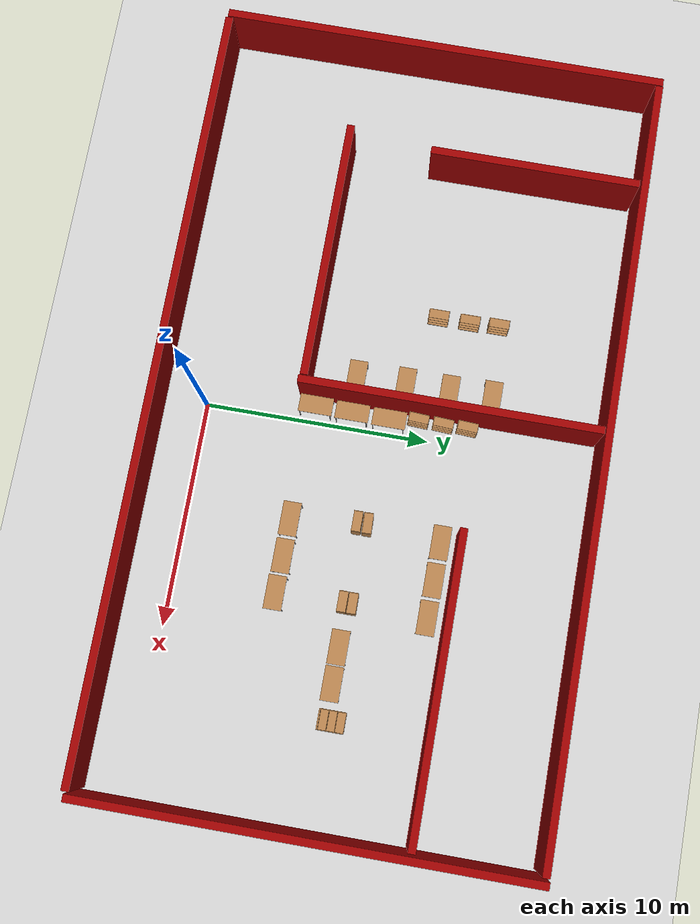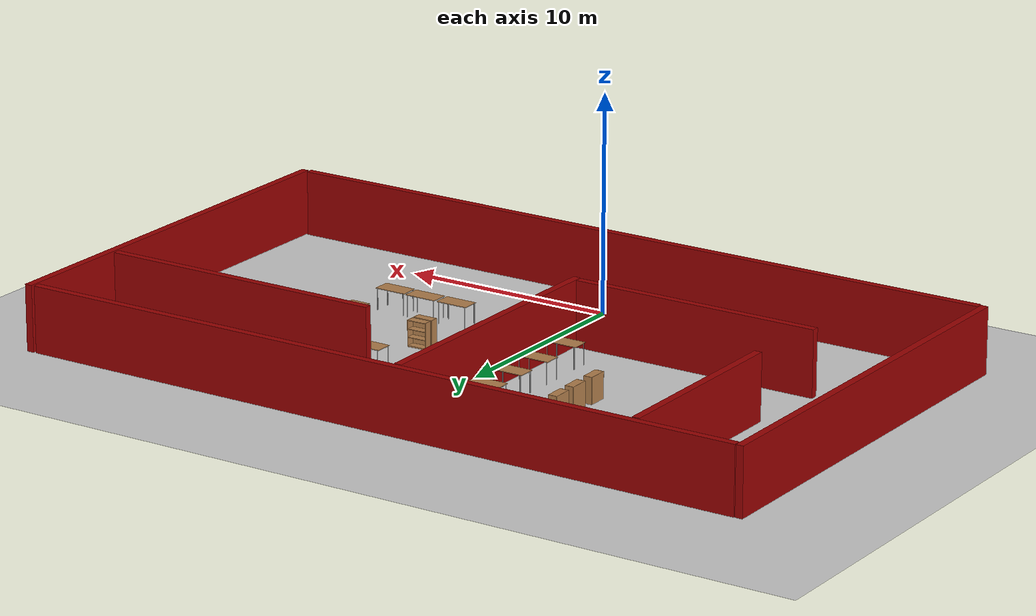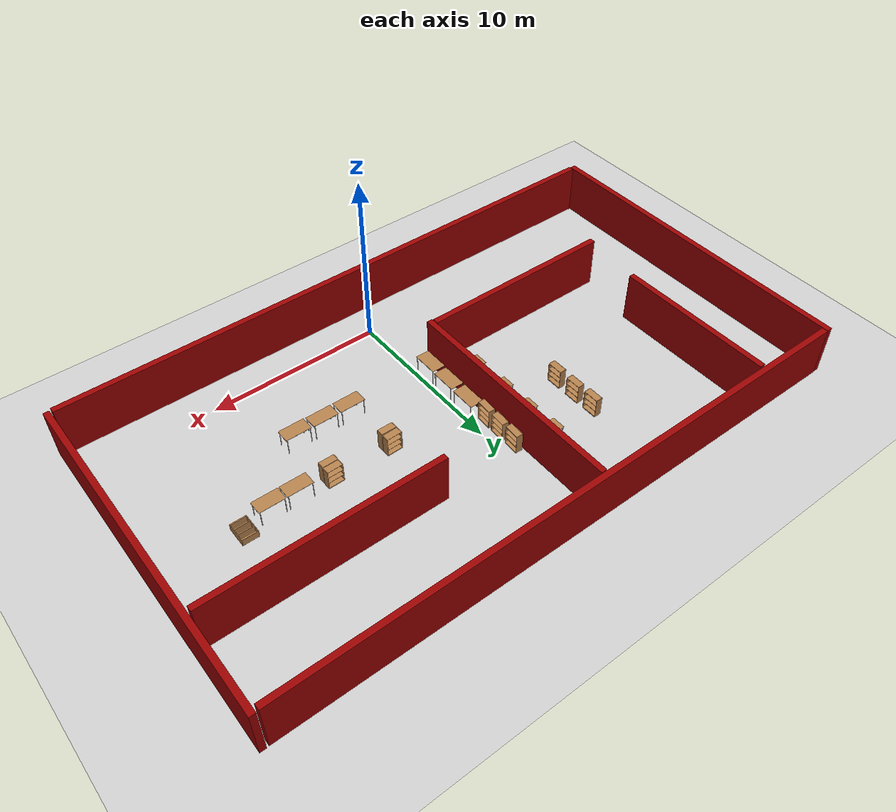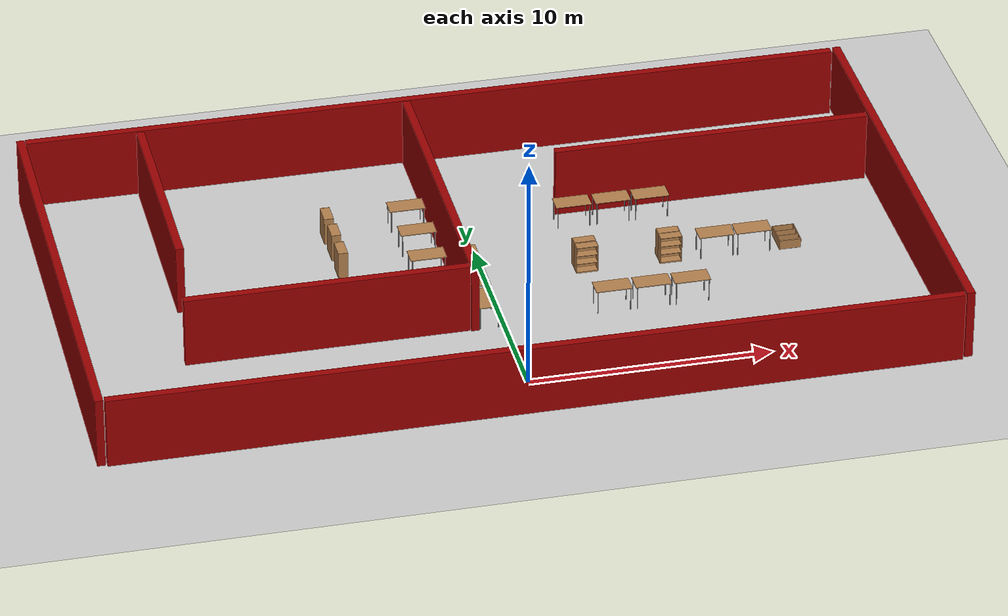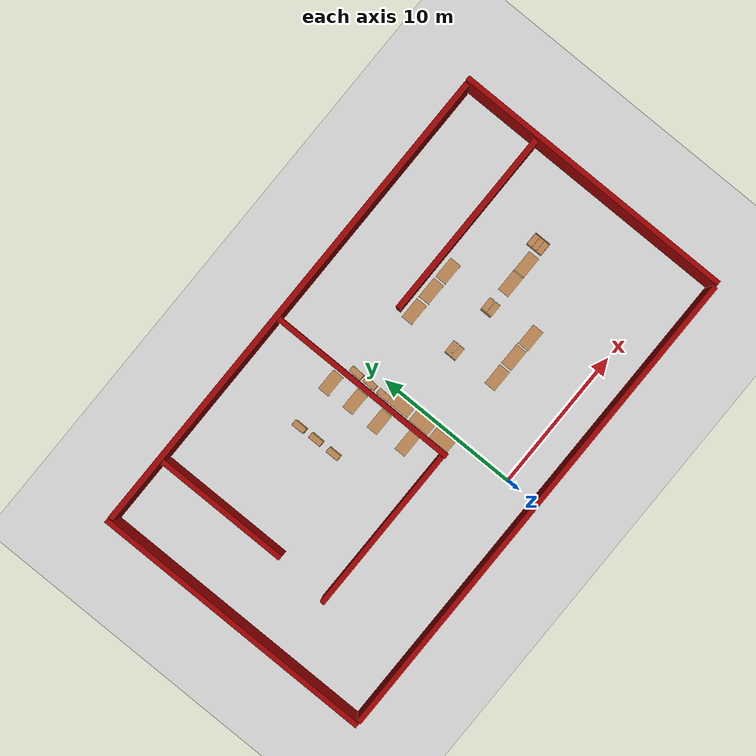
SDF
<sdf version="1.6">
 <world name="default">
  <light name="sun" type="directional">
   <pose>0 0 10 0 -0 0</pose>
   <diffuse>0.8 0.8 0.8 1</diffuse>
   <specular>0.2 0.2 0.2 1</specular>
   <attenuation>
    <range>1000</range>
    <constant>0.9</constant>
    <linear>0.01</linear>
    <quadratic>0.001</quadratic>
   </attenuation>
   <direction>-0.5 0.1 -0.9</direction>
  </light>
  <model name="ground_plane">
   <static>1</static>
   <link name="link">
    <collision name="collision">
     <geometry><plane><normal>0 0 1</normal><size>100 100</size></plane></geometry>
     <surface>
      <contact><collide_bitmask>65535</collide_bitmask></contact>
      <friction><ode><mu>100</mu><mu2>50</mu2></ode></friction>
     </surface>
    </collision>
    <visual name="visual">
     <cast_shadows>0</cast_shadows>
     <geometry><plane><normal>0 0 1</normal><size>100 100</size></plane></geometry>
     <material>
      <script><uri>file://media/materials/scripts/gazebo.material</uri><name>Gazebo/Grey</name></script>
     </material>
    </visual>
   </link>
  </model>
  <gravity>0 0 -9.8</gravity>
  <magnetic_field>6e-06 2.3e-05 -4.2e-05</magnetic_field>
  <atmosphere type="adiabatic"/>
  <physics name="default_physics" default="0" type="ode">
   <max_step_size>0.001</max_step_size>
   <real_time_factor>1</real_time_factor>
   <real_time_update_rate>1000</real_time_update_rate>
  </physics>
  <scene><ambient>0.4 0.4 0.4 1</ambient><background>0.7 0.7 0.7 1</background><shadows>1</shadows></scene>
  <audio><device>default</device></audio>
  <spherical_coordinates>
   <surface_model>EARTH_WGS84</surface_model>
   <latitude_deg>0</latitude_deg>
   <longitude_deg>0</longitude_deg>
   <elevation>0</elevation>
   <heading_deg>0</heading_deg>
  </spherical_coordinates>
  <model name="bookshelf">
   <static>1</static>
   <link name="link">
    <inertial><mass>1</mass></inertial>
    <collision name="back">
     <pose>0 0.005 0.6 0 -0 0</pose>
     <geometry><box><size>0.9 0.01 1.2</size></box></geometry>
    </collision>
    <visual name="visual1">
     <pose>0 0.005 0.6 0 -0 0</pose>
     <geometry><box><size>0.9 0.01 1.2</size></box></geometry>
     <material>
      <script><uri>file://media/materials/scripts/gazebo.material</uri><name>Gazebo/Wood</name></script>
     </material>
    </visual>
    <collision name="left_side">
     <pose>0.45 -0.195 0.6 0 -0 0</pose>
     <geometry><box><size>0.02 0.4 1.2</size></box></geometry>
    </collision>
    <visual name="visual2">
     <pose>0.45 -0.195 0.6 0 -0 0</pose>
     <geometry><box><size>0.02 0.4 1.2</size></box></geometry>
     <material>
      <script><uri>file://media/materials/scripts/gazebo.material</uri><name>Gazebo/Wood</name></script>
     </material>
    </visual>
    <collision name="right_side">
     <pose>-0.45 -0.195 0.6 0 -0 0</pose>
     <geometry><box><size>0.02 0.4 1.2</size></box></geometry>
    </collision>
    <visual name="visual3">
     <pose>-0.45 -0.195 0.6 0 -0 0</pose>
     <geometry><box><size>0.02 0.4 1.2</size></box></geometry>
     <material>
      <script><uri>file://media/materials/scripts/gazebo.material</uri><name>Gazebo/Wood</name></script>
     </material>
    </visual>
    <collision name="bottom">
     <pose>0 -0.195 0.03 0 -0 0</pose>
     <geometry><box><size>0.88 0.4 0.06</size></box></geometry>
    </collision>
    <visual name="visual4">
     <pose>0 -0.195 0.03 0 -0 0</pose>
     <geometry><box><size>0.88 0.4 0.06</size></box></geometry>
     <material>
      <script><uri>file://media/materials/scripts/gazebo.material</uri><name>Gazebo/Wood</name></script>
     </material>
    </visual>
    <collision name="top">
     <pose>0 -0.195 1.19 0 -0 0</pose>
     <geometry><box><size>0.88 0.4 0.02</size></box></geometry>
    </collision>
    <visual name="visual5">
     <pose>0 -0.195 1.19 0 -0 0</pose>
     <geometry><box><size>0.88 0.4 0.02</size></box></geometry>
     <material>
      <script><uri>file://media/materials/scripts/gazebo.material</uri><name>Gazebo/Wood</name></script>
     </material>
    </visual>
    <collision name="low_shelf">
     <pose>0 -0.195 0.43 0 -0 0</pose>
     <geometry><box><size>0.88 0.4 0.02</size></box></geometry>
    </collision>
    <visual name="visual6">
     <pose>0 -0.195 0.43 0 -0 0</pose>
     <geometry><box><size>0.88 0.4 0.02</size></box></geometry>
     <material>
      <script><uri>file://media/materials/scripts/gazebo.material</uri><name>Gazebo/Wood</name></script>
     </material>
    </visual>
    <collision name="high_shelf">
     <pose>0 -0.195 0.8 0 -0 0</pose>
     <geometry><box><size>0.88 0.4 0.02</size></box></geometry>
    </collision>
    <visual name="visual7">
     <pose>0 -0.195 0.8 0 -0 0</pose>
     <geometry><box><size>0.88 0.4 0.02</size></box></geometry>
     <material>
      <script><uri>file://media/materials/scripts/gazebo.material</uri><name>Gazebo/Wood</name></script>
     </material>
    </visual>
   </link>
   <pose>-0.972421 11.6801 0 0 -0 1.5196</pose>
  </model>
  <model name="table">
   <static>1</static>
   <link name="link">
    <collision name="surface">
     <pose>0 0 1 0 -0 0</pose>
     <geometry><box><size>1.5 0.8 0.03</size></box></geometry>
     <surface><friction><ode><mu>0.6</mu><mu2>0.6</mu2></ode></friction></surface>
    </collision>
    <visual name="visual1">
     <pose>0 0 1 0 -0 0</pose>
     <geometry><box><size>1.5 0.8 0.03</size></box></geometry>
     <material>
      <script><uri>file://media/materials/scripts/gazebo.material</uri><name>Gazebo/Wood</name></script>
     </material>
    </visual>
    <collision name="front_left_leg">
     <pose>0.68 0.38 0.5 0 -0 0</pose>
     <geometry><cylinder><radius>0.02</radius><length>1</length></cylinder></geometry>
    </collision>
    <visual name="front_left_leg">
     <pose>0.68 0.38 0.5 0 -0 0</pose>
     <geometry><cylinder><radius>0.02</radius><length>1</length></cylinder></geometry>
     <material>
      <script><uri>file://media/materials/scripts/gazebo.material</uri><name>Gazebo/Grey</name></script>
     </material>
    </visual>
    <collision name="front_right_leg">
     <pose>0.68 -0.38 0.5 0 -0 0</pose>
     <geometry><cylinder><radius>0.02</radius><length>1</length></cylinder></geometry>
    </collision>
    <visual name="front_right_leg">
     <pose>0.68 -0.38 0.5 0 -0 0</pose>
     <geometry><cylinder><radius>0.02</radius><length>1</length></cylinder></geometry>
     <material>
      <script><uri>file://media/materials/scripts/gazebo.material</uri><name>Gazebo/Grey</name></script>
     </material>
    </visual>
    <collision name="back_right_leg">
     <pose>-0.68 -0.38 0.5 0 -0 0</pose>
     <geometry><cylinder><radius>0.02</radius><length>1</length></cylinder></geometry>
    </collision>
    <visual name="back_right_leg">
     <pose>-0.68 -0.38 0.5 0 -0 0</pose>
     <geometry><cylinder><radius>0.02</radius><length>1</length></cylinder></geometry>
     <material>
      <script><uri>file://media/materials/scripts/gazebo.material</uri><name>Gazebo/Grey</name></script>
     </material>
    </visual>
    <collision name="back_left_leg">
     <pose>-0.68 0.38 0.5 0 -0 0</pose>
     <geometry><cylinder><radius>0.02</radius><length>1</length></cylinder></geometry>
    </collision>
    <visual name="back_left_leg">
     <pose>-0.68 0.38 0.5 0 -0 0</pose>
     <geometry><cylinder><radius>0.02</radius><length>1</length></cylinder></geometry>
     <material>
      <script><uri>file://media/materials/scripts/gazebo.material</uri><name>Gazebo/Grey</name></script>
     </material>
    </visual>
   </link>
   <pose>4.47207 11.3188 0 0 -0 0</pose>
  </model>
  <model name="table_0">
   <static>1</static>
   <link name="link">
    <collision name="surface">
     <pose>0 0 1 0 -0 0</pose>
     <geometry><box><size>1.5 0.8 0.03</size></box></geometry>
     <surface><friction><ode><mu>0.6</mu><mu2>0.6</mu2></ode></friction></surface>
    </collision>
    <visual name="visual1">
     <pose>0 0 1 0 -0 0</pose>
     <geometry><box><size>1.5 0.8 0.03</size></box></geometry>
     <material>
      <script><uri>file://media/materials/scripts/gazebo.material</uri><name>Gazebo/Wood</name></script>
     </material>
    </visual>
    <collision name="front_left_leg">
     <pose>0.68 0.38 0.5 0 -0 0</pose>
     <geometry><cylinder><radius>0.02</radius><length>1</length></cylinder></geometry>
    </collision>
    <visual name="front_left_leg">
     <pose>0.68 0.38 0.5 0 -0 0</pose>
     <geometry><cylinder><radius>0.02</radius><length>1</length></cylinder></geometry>
     <material>
      <script><uri>file://media/materials/scripts/gazebo.material</uri><name>Gazebo/Grey</name></script>
     </material>
    </visual>
    <collision name="front_right_leg">
     <pose>0.68 -0.38 0.5 0 -0 0</pose>
     <geometry><cylinder><radius>0.02</radius><length>1</length></cylinder></geometry>
    </collision>
    <visual name="front_right_leg">
     <pose>0.68 -0.38 0.5 0 -0 0</pose>
     <geometry><cylinder><radius>0.02</radius><length>1</length></cylinder></geometry>
     <material>
      <script><uri>file://media/materials/scripts/gazebo.material</uri><name>Gazebo/Grey</name></script>
     </material>
    </visual>
    <collision name="back_right_leg">
     <pose>-0.68 -0.38 0.5 0 -0 0</pose>
     <geometry><cylinder><radius>0.02</radius><length>1</length></cylinder></geometry>
    </collision>
    <visual name="back_right_leg">
     <pose>-0.68 -0.38 0.5 0 -0 0</pose>
     <geometry><cylinder><radius>0.02</radius><length>1</length></cylinder></geometry>
     <material>
      <script><uri>file://media/materials/scripts/gazebo.material</uri><name>Gazebo/Grey</name></script>
     </material>
    </visual>
    <collision name="back_left_leg">
     <pose>-0.68 0.38 0.5 0 -0 0</pose>
     <geometry><cylinder><radius>0.02</radius><length>1</length></cylinder></geometry>
    </collision>
    <visual name="back_left_leg">
     <pose>-0.68 0.38 0.5 0 -0 0</pose>
     <geometry><cylinder><radius>0.02</radius><length>1</length></cylinder></geometry>
     <material>
      <script><uri>file://media/materials/scripts/gazebo.material</uri><name>Gazebo/Grey</name></script>
     </material>
    </visual>
   </link>
   <pose>6.13122 11.3044 0 0 -0 0</pose>
  </model>
  <model name="table_1">
   <static>1</static>
   <link name="link">
    <collision name="surface">
     <pose>0 0 1 0 -0 0</pose>
     <geometry><box><size>1.5 0.8 0.03</size></box></geometry>
     <surface><friction><ode><mu>0.6</mu><mu2>0.6</mu2></ode></friction></surface>
    </collision>
    <visual name="visual1">
     <pose>0 0 1 0 -0 0</pose>
     <geometry><box><size>1.5 0.8 0.03</size></box></geometry>
     <material>
      <script><uri>file://media/materials/scripts/gazebo.material</uri><name>Gazebo/Wood</name></script>
     </material>
    </visual>
    <collision name="front_left_leg">
     <pose>0.68 0.38 0.5 0 -0 0</pose>
     <geometry><cylinder><radius>0.02</radius><length>1</length></cylinder></geometry>
    </collision>
    <visual name="front_left_leg">
     <pose>0.68 0.38 0.5 0 -0 0</pose>
     <geometry><cylinder><radius>0.02</radius><length>1</length></cylinder></geometry>
     <material>
      <script><uri>file://media/materials/scripts/gazebo.material</uri><name>Gazebo/Grey</name></script>
     </material>
    </visual>
    <collision name="front_right_leg">
     <pose>0.68 -0.38 0.5 0 -0 0</pose>
     <geometry><cylinder><radius>0.02</radius><length>1</length></cylinder></geometry>
    </collision>
    <visual name="front_right_leg">
     <pose>0.68 -0.38 0.5 0 -0 0</pose>
     <geometry><cylinder><radius>0.02</radius><length>1</length></cylinder></geometry>
     <material>
      <script><uri>file://media/materials/scripts/gazebo.material</uri><name>Gazebo/Grey</name></script>
     </material>
    </visual>
    <collision name="back_right_leg">
     <pose>-0.68 -0.38 0.5 0 -0 0</pose>
     <geometry><cylinder><radius>0.02</radius><length>1</length></cylinder></geometry>
    </collision>
    <visual name="back_right_leg">
     <pose>-0.68 -0.38 0.5 0 -0 0</pose>
     <geometry><cylinder><radius>0.02</radius><length>1</length></cylinder></geometry>
     <material>
      <script><uri>file://media/materials/scripts/gazebo.material</uri><name>Gazebo/Grey</name></script>
     </material>
    </visual>
    <collision name="back_left_leg">
     <pose>-0.68 0.38 0.5 0 -0 0</pose>
     <geometry><cylinder><radius>0.02</radius><length>1</length></cylinder></geometry>
    </collision>
    <visual name="back_left_leg">
     <pose>-0.68 0.38 0.5 0 -0 0</pose>
     <geometry><cylinder><radius>0.02</radius><length>1</length></cylinder></geometry>
     <material>
      <script><uri>file://media/materials/scripts/gazebo.material</uri><name>Gazebo/Grey</name></script>
     </material>
    </visual>
   </link>
   <pose>7.77291 11.2867 0 0 -0 0</pose>
  </model>
  <model name="bookshelf_0">
   <static>1</static>
   <link name="link">
    <inertial><mass>1</mass></inertial>
    <collision name="back">
     <pose>0 0.005 0.6 0 -0 0</pose>
     <geometry><box><size>0.9 0.01 1.2</size></box></geometry>
    </collision>
    <visual name="visual1">
     <pose>0 0.005 0.6 0 -0 0</pose>
     <geometry><box><size>0.9 0.01 1.2</size></box></geometry>
     <material>
      <script><uri>file://media/materials/scripts/gazebo.material</uri><name>Gazebo/Wood</name></script>
     </material>
    </visual>
    <collision name="left_side">
     <pose>0.45 -0.195 0.6 0 -0 0</pose>
     <geometry><box><size>0.02 0.4 1.2</size></box></geometry>
    </collision>
    <visual name="visual2">
     <pose>0.45 -0.195 0.6 0 -0 0</pose>
     <geometry><box><size>0.02 0.4 1.2</size></box></geometry>
     <material>
      <script><uri>file://media/materials/scripts/gazebo.material</uri><name>Gazebo/Wood</name></script>
     </material>
    </visual>
    <collision name="right_side">
     <pose>-0.45 -0.195 0.6 0 -0 0</pose>
     <geometry><box><size>0.02 0.4 1.2</size></box></geometry>
    </collision>
    <visual name="visual3">
     <pose>-0.45 -0.195 0.6 0 -0 0</pose>
     <geometry><box><size>0.02 0.4 1.2</size></box></geometry>
     <material>
      <script><uri>file://media/materials/scripts/gazebo.material</uri><name>Gazebo/Wood</name></script>
     </material>
    </visual>
    <collision name="bottom">
     <pose>0 -0.195 0.03 0 -0 0</pose>
     <geometry><box><size>0.88 0.4 0.06</size></box></geometry>
    </collision>
    <visual name="visual4">
     <pose>0 -0.195 0.03 0 -0 0</pose>
     <geometry><box><size>0.88 0.4 0.06</size></box></geometry>
     <material>
      <script><uri>file://media/materials/scripts/gazebo.material</uri><name>Gazebo/Wood</name></script>
     </material>
    </visual>
    <collision name="top">
     <pose>0 -0.195 1.19 0 -0 0</pose>
     <geometry><box><size>0.88 0.4 0.02</size></box></geometry>
    </collision>
    <visual name="visual5">
     <pose>0 -0.195 1.19 0 -0 0</pose>
     <geometry><box><size>0.88 0.4 0.02</size></box></geometry>
     <material>
      <script><uri>file://media/materials/scripts/gazebo.material</uri><name>Gazebo/Wood</name></script>
     </material>
    </visual>
    <collision name="low_shelf">
     <pose>0 -0.195 0.43 0 -0 0</pose>
     <geometry><box><size>0.88 0.4 0.02</size></box></geometry>
    </collision>
    <visual name="visual6">
     <pose>0 -0.195 0.43 0 -0 0</pose>
     <geometry><box><size>0.88 0.4 0.02</size></box></geometry>
     <material>
      <script><uri>file://media/materials/scripts/gazebo.material</uri><name>Gazebo/Wood</name></script>
     </material>
    </visual>
    <collision name="high_shelf">
     <pose>0 -0.195 0.8 0 -0 0</pose>
     <geometry><box><size>0.88 0.4 0.02</size></box></geometry>
    </collision>
    <visual name="visual7">
     <pose>0 -0.195 0.8 0 -0 0</pose>
     <geometry><box><size>0.88 0.4 0.02</size></box></geometry>
     <material>
      <script><uri>file://media/materials/scripts/gazebo.material</uri><name>Gazebo/Wood</name></script>
     </material>
    </visual>
   </link>
   <pose>4.19826 7.86645 0 0 0 -3.11809</pose>
  </model>
  <model name="bookshelf_1">
   <static>1</static>
   <link name="link">
    <inertial><mass>1</mass></inertial>
    <collision name="back">
     <pose>0 0.005 0.6 0 -0 0</pose>
     <geometry><box><size>0.9 0.01 1.2</size></box></geometry>
    </collision>
    <visual name="visual1">
     <pose>0 0.005 0.6 0 -0 0</pose>
     <geometry><box><size>0.9 0.01 1.2</size></box></geometry>
     <material>
      <script><uri>file://media/materials/scripts/gazebo.material</uri><name>Gazebo/Wood</name></script>
     </material>
    </visual>
    <collision name="left_side">
     <pose>0.45 -0.195 0.6 0 -0 0</pose>
     <geometry><box><size>0.02 0.4 1.2</size></box></geometry>
    </collision>
    <visual name="visual2">
     <pose>0.45 -0.195 0.6 0 -0 0</pose>
     <geometry><box><size>0.02 0.4 1.2</size></box></geometry>
     <material>
      <script><uri>file://media/materials/scripts/gazebo.material</uri><name>Gazebo/Wood</name></script>
     </material>
    </visual>
    <collision name="right_side">
     <pose>-0.45 -0.195 0.6 0 -0 0</pose>
     <geometry><box><size>0.02 0.4 1.2</size></box></geometry>
    </collision>
    <visual name="visual3">
     <pose>-0.45 -0.195 0.6 0 -0 0</pose>
     <geometry><box><size>0.02 0.4 1.2</size></box></geometry>
     <material>
      <script><uri>file://media/materials/scripts/gazebo.material</uri><name>Gazebo/Wood</name></script>
     </material>
    </visual>
    <collision name="bottom">
     <pose>0 -0.195 0.03 0 -0 0</pose>
     <geometry><box><size>0.88 0.4 0.06</size></box></geometry>
    </collision>
    <visual name="visual4">
     <pose>0 -0.195 0.03 0 -0 0</pose>
     <geometry><box><size>0.88 0.4 0.06</size></box></geometry>
     <material>
      <script><uri>file://media/materials/scripts/gazebo.material</uri><name>Gazebo/Wood</name></script>
     </material>
    </visual>
    <collision name="top">
     <pose>0 -0.195 1.19 0 -0 0</pose>
     <geometry><box><size>0.88 0.4 0.02</size></box></geometry>
    </collision>
    <visual name="visual5">
     <pose>0 -0.195 1.19 0 -0 0</pose>
     <geometry><box><size>0.88 0.4 0.02</size></box></geometry>
     <material>
      <script><uri>file://media/materials/scripts/gazebo.material</uri><name>Gazebo/Wood</name></script>
     </material>
    </visual>
    <collision name="low_shelf">
     <pose>0 -0.195 0.43 0 -0 0</pose>
     <geometry><box><size>0.88 0.4 0.02</size></box></geometry>
    </collision>
    <visual name="visual6">
     <pose>0 -0.195 0.43 0 -0 0</pose>
     <geometry><box><size>0.88 0.4 0.02</size></box></geometry>
     <material>
      <script><uri>file://media/materials/scripts/gazebo.material</uri><name>Gazebo/Wood</name></script>
     </material>
    </visual>
    <collision name="high_shelf">
     <pose>0 -0.195 0.8 0 -0 0</pose>
     <geometry><box><size>0.88 0.4 0.02</size></box></geometry>
    </collision>
    <visual name="visual7">
     <pose>0 -0.195 0.8 0 -0 0</pose>
     <geometry><box><size>0.88 0.4 0.02</size></box></geometry>
     <material>
      <script><uri>file://media/materials/scripts/gazebo.material</uri><name>Gazebo/Wood</name></script>
     </material>
    </visual>
   </link>
   <pose>7.71048 7.81574 0 0 0 -3.1319</pose>
  </model>
  <model name="bookshelf_2">
   <static>1</static>
   <link name="link">
    <inertial><mass>1</mass></inertial>
    <collision name="back">
     <pose>0 0.005 0.6 0 -0 0</pose>
     <geometry><box><size>0.9 0.01 1.2</size></box></geometry>
    </collision>
    <visual name="visual1">
     <pose>0 0.005 0.6 0 -0 0</pose>
     <geometry><box><size>0.9 0.01 1.2</size></box></geometry>
     <material>
      <script><uri>file://media/materials/scripts/gazebo.material</uri><name>Gazebo/Wood</name></script>
     </material>
    </visual>
    <collision name="left_side">
     <pose>0.45 -0.195 0.6 0 -0 0</pose>
     <geometry><box><size>0.02 0.4 1.2</size></box></geometry>
    </collision>
    <visual name="visual2">
     <pose>0.45 -0.195 0.6 0 -0 0</pose>
     <geometry><box><size>0.02 0.4 1.2</size></box></geometry>
     <material>
      <script><uri>file://media/materials/scripts/gazebo.material</uri><name>Gazebo/Wood</name></script>
     </material>
    </visual>
    <collision name="right_side">
     <pose>-0.45 -0.195 0.6 0 -0 0</pose>
     <geometry><box><size>0.02 0.4 1.2</size></box></geometry>
    </collision>
    <visual name="visual3">
     <pose>-0.45 -0.195 0.6 0 -0 0</pose>
     <geometry><box><size>0.02 0.4 1.2</size></box></geometry>
     <material>
      <script><uri>file://media/materials/scripts/gazebo.material</uri><name>Gazebo/Wood</name></script>
     </material>
    </visual>
    <collision name="bottom">
     <pose>0 -0.195 0.03 0 -0 0</pose>
     <geometry><box><size>0.88 0.4 0.06</size></box></geometry>
    </collision>
    <visual name="visual4">
     <pose>0 -0.195 0.03 0 -0 0</pose>
     <geometry><box><size>0.88 0.4 0.06</size></box></geometry>
     <material>
      <script><uri>file://media/materials/scripts/gazebo.material</uri><name>Gazebo/Wood</name></script>
     </material>
    </visual>
    <collision name="top">
     <pose>0 -0.195 1.19 0 -0 0</pose>
     <geometry><box><size>0.88 0.4 0.02</size></box></geometry>
    </collision>
    <visual name="visual5">
     <pose>0 -0.195 1.19 0 -0 0</pose>
     <geometry><box><size>0.88 0.4 0.02</size></box></geometry>
     <material>
      <script><uri>file://media/materials/scripts/gazebo.material</uri><name>Gazebo/Wood</name></script>
     </material>
    </visual>
    <collision name="low_shelf">
     <pose>0 -0.195 0.43 0 -0 0</pose>
     <geometry><box><size>0.88 0.4 0.02</size></box></geometry>
    </collision>
    <visual name="visual6">
     <pose>0 -0.195 0.43 0 -0 0</pose>
     <geometry><box><size>0.88 0.4 0.02</size></box></geometry>
     <material>
      <script><uri>file://media/materials/scripts/gazebo.material</uri><name>Gazebo/Wood</name></script>
     </material>
    </visual>
    <collision name="high_shelf">
     <pose>0 -0.195 0.8 0 -0 0</pose>
     <geometry><box><size>0.88 0.4 0.02</size></box></geometry>
    </collision>
    <visual name="visual7">
     <pose>0 -0.195 0.8 0 -0 0</pose>
     <geometry><box><size>0.88 0.4 0.02</size></box></geometry>
     <material>
      <script><uri>file://media/materials/scripts/gazebo.material</uri><name>Gazebo/Wood</name></script>
     </material>
    </visual>
   </link>
   <pose>4.19078 7.7911 0 0 -0 0</pose>
  </model>
  <model name="bookshelf_3">
   <static>1</static>
   <link name="link">
    <inertial><mass>1</mass></inertial>
    <collision name="back">
     <pose>0 0.005 0.6 0 -0 0</pose>
     <geometry><box><size>0.9 0.01 1.2</size></box></geometry>
    </collision>
    <visual name="visual1">
     <pose>0 0.005 0.6 0 -0 0</pose>
     <geometry><box><size>0.9 0.01 1.2</size></box></geometry>
     <material>
      <script><uri>file://media/materials/scripts/gazebo.material</uri><name>Gazebo/Wood</name></script>
     </material>
    </visual>
    <collision name="left_side">
     <pose>0.45 -0.195 0.6 0 -0 0</pose>
     <geometry><box><size>0.02 0.4 1.2</size></box></geometry>
    </collision>
    <visual name="visual2">
     <pose>0.45 -0.195 0.6 0 -0 0</pose>
     <geometry><box><size>0.02 0.4 1.2</size></box></geometry>
     <material>
      <script><uri>file://media/materials/scripts/gazebo.material</uri><name>Gazebo/Wood</name></script>
     </material>
    </visual>
    <collision name="right_side">
     <pose>-0.45 -0.195 0.6 0 -0 0</pose>
     <geometry><box><size>0.02 0.4 1.2</size></box></geometry>
    </collision>
    <visual name="visual3">
     <pose>-0.45 -0.195 0.6 0 -0 0</pose>
     <geometry><box><size>0.02 0.4 1.2</size></box></geometry>
     <material>
      <script><uri>file://media/materials/scripts/gazebo.material</uri><name>Gazebo/Wood</name></script>
     </material>
    </visual>
    <collision name="bottom">
     <pose>0 -0.195 0.03 0 -0 0</pose>
     <geometry><box><size>0.88 0.4 0.06</size></box></geometry>
    </collision>
    <visual name="visual4">
     <pose>0 -0.195 0.03 0 -0 0</pose>
     <geometry><box><size>0.88 0.4 0.06</size></box></geometry>
     <material>
      <script><uri>file://media/materials/scripts/gazebo.material</uri><name>Gazebo/Wood</name></script>
     </material>
    </visual>
    <collision name="top">
     <pose>0 -0.195 1.19 0 -0 0</pose>
     <geometry><box><size>0.88 0.4 0.02</size></box></geometry>
    </collision>
    <visual name="visual5">
     <pose>0 -0.195 1.19 0 -0 0</pose>
     <geometry><box><size>0.88 0.4 0.02</size></box></geometry>
     <material>
      <script><uri>file://media/materials/scripts/gazebo.material</uri><name>Gazebo/Wood</name></script>
     </material>
    </visual>
    <collision name="low_shelf">
     <pose>0 -0.195 0.43 0 -0 0</pose>
     <geometry><box><size>0.88 0.4 0.02</size></box></geometry>
    </collision>
    <visual name="visual6">
     <pose>0 -0.195 0.43 0 -0 0</pose>
     <geometry><box><size>0.88 0.4 0.02</size></box></geometry>
     <material>
      <script><uri>file://media/materials/scripts/gazebo.material</uri><name>Gazebo/Wood</name></script>
     </material>
    </visual>
    <collision name="high_shelf">
     <pose>0 -0.195 0.8 0 -0 0</pose>
     <geometry><box><size>0.88 0.4 0.02</size></box></geometry>
    </collision>
    <visual name="visual7">
     <pose>0 -0.195 0.8 0 -0 0</pose>
     <geometry><box><size>0.88 0.4 0.02</size></box></geometry>
     <material>
      <script><uri>file://media/materials/scripts/gazebo.material</uri><name>Gazebo/Wood</name></script>
     </material>
    </visual>
   </link>
   <pose>7.70642 7.76994 0 0 -0 0</pose>
  </model>
  <model name="table_2">
   <static>1</static>
   <link name="link">
    <collision name="surface">
     <pose>0 0 1 0 -0 0</pose>
     <geometry><box><size>1.5 0.8 0.03</size></box></geometry>
     <surface><friction><ode><mu>0.6</mu><mu2>0.6</mu2></ode></friction></surface>
    </collision>
    <visual name="visual1">
     <pose>0 0 1 0 -0 0</pose>
     <geometry><box><size>1.5 0.8 0.03</size></box></geometry>
     <material>
      <script><uri>file://media/materials/scripts/gazebo.material</uri><name>Gazebo/Wood</name></script>
     </material>
    </visual>
    <collision name="front_left_leg">
     <pose>0.68 0.38 0.5 0 -0 0</pose>
     <geometry><cylinder><radius>0.02</radius><length>1</length></cylinder></geometry>
    </collision>
    <visual name="front_left_leg">
     <pose>0.68 0.38 0.5 0 -0 0</pose>
     <geometry><cylinder><radius>0.02</radius><length>1</length></cylinder></geometry>
     <material>
      <script><uri>file://media/materials/scripts/gazebo.material</uri><name>Gazebo/Grey</name></script>
     </material>
    </visual>
    <collision name="front_right_leg">
     <pose>0.68 -0.38 0.5 0 -0 0</pose>
     <geometry><cylinder><radius>0.02</radius><length>1</length></cylinder></geometry>
    </collision>
    <visual name="front_right_leg">
     <pose>0.68 -0.38 0.5 0 -0 0</pose>
     <geometry><cylinder><radius>0.02</radius><length>1</length></cylinder></geometry>
     <material>
      <script><uri>file://media/materials/scripts/gazebo.material</uri><name>Gazebo/Grey</name></script>
     </material>
    </visual>
    <collision name="back_right_leg">
     <pose>-0.68 -0.38 0.5 0 -0 0</pose>
     <geometry><cylinder><radius>0.02</radius><length>1</length></cylinder></geometry>
    </collision>
    <visual name="back_right_leg">
     <pose>-0.68 -0.38 0.5 0 -0 0</pose>
     <geometry><cylinder><radius>0.02</radius><length>1</length></cylinder></geometry>
     <material>
      <script><uri>file://media/materials/scripts/gazebo.material</uri><name>Gazebo/Grey</name></script>
     </material>
    </visual>
    <collision name="back_left_leg">
     <pose>-0.68 0.38 0.5 0 -0 0</pose>
     <geometry><cylinder><radius>0.02</radius><length>1</length></cylinder></geometry>
    </collision>
    <visual name="back_left_leg">
     <pose>-0.68 0.38 0.5 0 -0 0</pose>
     <geometry><cylinder><radius>0.02</radius><length>1</length></cylinder></geometry>
     <material>
      <script><uri>file://media/materials/scripts/gazebo.material</uri><name>Gazebo/Grey</name></script>
     </material>
    </visual>
   </link>
   <pose>4.56115 4.67955 0 0 -0 0</pose>
  </model>
  <model name="table_3">
   <static>1</static>
   <link name="link">
    <collision name="surface">
     <pose>0 0 1 0 -0 0</pose>
     <geometry><box><size>1.5 0.8 0.03</size></box></geometry>
     <surface><friction><ode><mu>0.6</mu><mu2>0.6</mu2></ode></friction></surface>
    </collision>
    <visual name="visual1">
     <pose>0 0 1 0 -0 0</pose>
     <geometry><box><size>1.5 0.8 0.03</size></box></geometry>
     <material>
      <script><uri>file://media/materials/scripts/gazebo.material</uri><name>Gazebo/Wood</name></script>
     </material>
    </visual>
    <collision name="front_left_leg">
     <pose>0.68 0.38 0.5 0 -0 0</pose>
     <geometry><cylinder><radius>0.02</radius><length>1</length></cylinder></geometry>
    </collision>
    <visual name="front_left_leg">
     <pose>0.68 0.38 0.5 0 -0 0</pose>
     <geometry><cylinder><radius>0.02</radius><length>1</length></cylinder></geometry>
     <material>
      <script><uri>file://media/materials/scripts/gazebo.material</uri><name>Gazebo/Grey</name></script>
     </material>
    </visual>
    <collision name="front_right_leg">
     <pose>0.68 -0.38 0.5 0 -0 0</pose>
     <geometry><cylinder><radius>0.02</radius><length>1</length></cylinder></geometry>
    </collision>
    <visual name="front_right_leg">
     <pose>0.68 -0.38 0.5 0 -0 0</pose>
     <geometry><cylinder><radius>0.02</radius><length>1</length></cylinder></geometry>
     <material>
      <script><uri>file://media/materials/scripts/gazebo.material</uri><name>Gazebo/Grey</name></script>
     </material>
    </visual>
    <collision name="back_right_leg">
     <pose>-0.68 -0.38 0.5 0 -0 0</pose>
     <geometry><cylinder><radius>0.02</radius><length>1</length></cylinder></geometry>
    </collision>
    <visual name="back_right_leg">
     <pose>-0.68 -0.38 0.5 0 -0 0</pose>
     <geometry><cylinder><radius>0.02</radius><length>1</length></cylinder></geometry>
     <material>
      <script><uri>file://media/materials/scripts/gazebo.material</uri><name>Gazebo/Grey</name></script>
     </material>
    </visual>
    <collision name="back_left_leg">
     <pose>-0.68 0.38 0.5 0 -0 0</pose>
     <geometry><cylinder><radius>0.02</radius><length>1</length></cylinder></geometry>
    </collision>
    <visual name="back_left_leg">
     <pose>-0.68 0.38 0.5 0 -0 0</pose>
     <geometry><cylinder><radius>0.02</radius><length>1</length></cylinder></geometry>
     <material>
      <script><uri>file://media/materials/scripts/gazebo.material</uri><name>Gazebo/Grey</name></script>
     </material>
    </visual>
   </link>
   <pose>6.19952 4.67486 0 0 -0 0</pose>
  </model>
  <model name="table_4">
   <static>1</static>
   <link name="link">
    <collision name="surface">
     <pose>0 0 1 0 -0 0</pose>
     <geometry><box><size>1.5 0.8 0.03</size></box></geometry>
     <surface><friction><ode><mu>0.6</mu><mu2>0.6</mu2></ode></friction></surface>
    </collision>
    <visual name="visual1">
     <pose>0 0 1 0 -0 0</pose>
     <geometry><box><size>1.5 0.8 0.03</size></box></geometry>
     <material>
      <script><uri>file://media/materials/scripts/gazebo.material</uri><name>Gazebo/Wood</name></script>
     </material>
    </visual>
    <collision name="front_left_leg">
     <pose>0.68 0.38 0.5 0 -0 0</pose>
     <geometry><cylinder><radius>0.02</radius><length>1</length></cylinder></geometry>
    </collision>
    <visual name="front_left_leg">
     <pose>0.68 0.38 0.5 0 -0 0</pose>
     <geometry><cylinder><radius>0.02</radius><length>1</length></cylinder></geometry>
     <material>
      <script><uri>file://media/materials/scripts/gazebo.material</uri><name>Gazebo/Grey</name></script>
     </material>
    </visual>
    <collision name="front_right_leg">
     <pose>0.68 -0.38 0.5 0 -0 0</pose>
     <geometry><cylinder><radius>0.02</radius><length>1</length></cylinder></geometry>
    </collision>
    <visual name="front_right_leg">
     <pose>0.68 -0.38 0.5 0 -0 0</pose>
     <geometry><cylinder><radius>0.02</radius><length>1</length></cylinder></geometry>
     <material>
      <script><uri>file://media/materials/scripts/gazebo.material</uri><name>Gazebo/Grey</name></script>
     </material>
    </visual>
    <collision name="back_right_leg">
     <pose>-0.68 -0.38 0.5 0 -0 0</pose>
     <geometry><cylinder><radius>0.02</radius><length>1</length></cylinder></geometry>
    </collision>
    <visual name="back_right_leg">
     <pose>-0.68 -0.38 0.5 0 -0 0</pose>
     <geometry><cylinder><radius>0.02</radius><length>1</length></cylinder></geometry>
     <material>
      <script><uri>file://media/materials/scripts/gazebo.material</uri><name>Gazebo/Grey</name></script>
     </material>
    </visual>
    <collision name="back_left_leg">
     <pose>-0.68 0.38 0.5 0 -0 0</pose>
     <geometry><cylinder><radius>0.02</radius><length>1</length></cylinder></geometry>
    </collision>
    <visual name="back_left_leg">
     <pose>-0.68 0.38 0.5 0 -0 0</pose>
     <geometry><cylinder><radius>0.02</radius><length>1</length></cylinder></geometry>
     <material>
      <script><uri>file://media/materials/scripts/gazebo.material</uri><name>Gazebo/Grey</name></script>
     </material>
    </visual>
   </link>
   <pose>7.81299 4.6334 0 0 -0 0</pose>
  </model>
  <model name="table_5">
   <static>1</static>
   <link name="link">
    <collision name="surface">
     <pose>0 0 1 0 -0 0</pose>
     <geometry><box><size>1.5 0.8 0.03</size></box></geometry>
     <surface><friction><ode><mu>0.6</mu><mu2>0.6</mu2></ode></friction></surface>
    </collision>
    <visual name="visual1">
     <pose>0 0 1 0 -0 0</pose>
     <geometry><box><size>1.5 0.8 0.03</size></box></geometry>
     <material>
      <script><uri>file://media/materials/scripts/gazebo.material</uri><name>Gazebo/Wood</name></script>
     </material>
    </visual>
    <collision name="front_left_leg">
     <pose>0.68 0.38 0.5 0 -0 0</pose>
     <geometry><cylinder><radius>0.02</radius><length>1</length></cylinder></geometry>
    </collision>
    <visual name="front_left_leg">
     <pose>0.68 0.38 0.5 0 -0 0</pose>
     <geometry><cylinder><radius>0.02</radius><length>1</length></cylinder></geometry>
     <material>
      <script><uri>file://media/materials/scripts/gazebo.material</uri><name>Gazebo/Grey</name></script>
     </material>
    </visual>
    <collision name="front_right_leg">
     <pose>0.68 -0.38 0.5 0 -0 0</pose>
     <geometry><cylinder><radius>0.02</radius><length>1</length></cylinder></geometry>
    </collision>
    <visual name="front_right_leg">
     <pose>0.68 -0.38 0.5 0 -0 0</pose>
     <geometry><cylinder><radius>0.02</radius><length>1</length></cylinder></geometry>
     <material>
      <script><uri>file://media/materials/scripts/gazebo.material</uri><name>Gazebo/Grey</name></script>
     </material>
    </visual>
    <collision name="back_right_leg">
     <pose>-0.68 -0.38 0.5 0 -0 0</pose>
     <geometry><cylinder><radius>0.02</radius><length>1</length></cylinder></geometry>
    </collision>
    <visual name="back_right_leg">
     <pose>-0.68 -0.38 0.5 0 -0 0</pose>
     <geometry><cylinder><radius>0.02</radius><length>1</length></cylinder></geometry>
     <material>
      <script><uri>file://media/materials/scripts/gazebo.material</uri><name>Gazebo/Grey</name></script>
     </material>
    </visual>
    <collision name="back_left_leg">
     <pose>-0.68 0.38 0.5 0 -0 0</pose>
     <geometry><cylinder><radius>0.02</radius><length>1</length></cylinder></geometry>
    </collision>
    <visual name="back_left_leg">
     <pose>-0.68 0.38 0.5 0 -0 0</pose>
     <geometry><cylinder><radius>0.02</radius><length>1</length></cylinder></geometry>
     <material>
      <script><uri>file://media/materials/scripts/gazebo.material</uri><name>Gazebo/Grey</name></script>
     </material>
    </visual>
   </link>
   <pose>9.6451 7.74871 0 0 -0 0</pose>
  </model>
  <model name="table_6">
   <static>1</static>
   <link name="link">
    <collision name="surface">
     <pose>0 0 1 0 -0 0</pose>
     <geometry><box><size>1.5 0.8 0.03</size></box></geometry>
     <surface><friction><ode><mu>0.6</mu><mu2>0.6</mu2></ode></friction></surface>
    </collision>
    <visual name="visual1">
     <pose>0 0 1 0 -0 0</pose>
     <geometry><box><size>1.5 0.8 0.03</size></box></geometry>
     <material>
      <script><uri>file://media/materials/scripts/gazebo.material</uri><name>Gazebo/Wood</name></script>
     </material>
    </visual>
    <collision name="front_left_leg">
     <pose>0.68 0.38 0.5 0 -0 0</pose>
     <geometry><cylinder><radius>0.02</radius><length>1</length></cylinder></geometry>
    </collision>
    <visual name="front_left_leg">
     <pose>0.68 0.38 0.5 0 -0 0</pose>
     <geometry><cylinder><radius>0.02</radius><length>1</length></cylinder></geometry>
     <material>
      <script><uri>file://media/materials/scripts/gazebo.material</uri><name>Gazebo/Grey</name></script>
     </material>
    </visual>
    <collision name="front_right_leg">
     <pose>0.68 -0.38 0.5 0 -0 0</pose>
     <geometry><cylinder><radius>0.02</radius><length>1</length></cylinder></geometry>
    </collision>
    <visual name="front_right_leg">
     <pose>0.68 -0.38 0.5 0 -0 0</pose>
     <geometry><cylinder><radius>0.02</radius><length>1</length></cylinder></geometry>
     <material>
      <script><uri>file://media/materials/scripts/gazebo.material</uri><name>Gazebo/Grey</name></script>
     </material>
    </visual>
    <collision name="back_right_leg">
     <pose>-0.68 -0.38 0.5 0 -0 0</pose>
     <geometry><cylinder><radius>0.02</radius><length>1</length></cylinder></geometry>
    </collision>
    <visual name="back_right_leg">
     <pose>-0.68 -0.38 0.5 0 -0 0</pose>
     <geometry><cylinder><radius>0.02</radius><length>1</length></cylinder></geometry>
     <material>
      <script><uri>file://media/materials/scripts/gazebo.material</uri><name>Gazebo/Grey</name></script>
     </material>
    </visual>
    <collision name="back_left_leg">
     <pose>-0.68 0.38 0.5 0 -0 0</pose>
     <geometry><cylinder><radius>0.02</radius><length>1</length></cylinder></geometry>
    </collision>
    <visual name="back_left_leg">
     <pose>-0.68 0.38 0.5 0 -0 0</pose>
     <geometry><cylinder><radius>0.02</radius><length>1</length></cylinder></geometry>
     <material>
      <script><uri>file://media/materials/scripts/gazebo.material</uri><name>Gazebo/Grey</name></script>
     </material>
    </visual>
   </link>
   <pose>11.2038 7.74465 0 0 -0 0</pose>
  </model>
  <model name="bookshelf_4">
   <link name="link">
    <inertial>
     <mass>1</mass>
     <inertia><ixx>1</ixx><ixy>0</ixy><ixz>0</ixz><iyy>1</iyy><iyz>0</iyz><izz>1</izz></inertia>
    </inertial>
    <visual name="visual1">
     <pose>0 0.005 0.6 0 -0 0</pose>
     <geometry><box><size>0.9 0.01 1.2</size></box></geometry>
     <material>
      <script><uri>file://media/materials/scripts/gazebo.material</uri><name>Gazebo/Wood</name></script>
      <shader type="vertex"><normal_map>__default__</normal_map></shader>
     </material>
    </visual>
    <visual name="visual2">
     <pose>0.45 -0.195 0.6 0 -0 0</pose>
     <geometry><box><size>0.02 0.4 1.2</size></box></geometry>
     <material>
      <script><uri>file://media/materials/scripts/gazebo.material</uri><name>Gazebo/Wood</name></script>
      <shader type="vertex"><normal_map>__default__</normal_map></shader>
     </material>
    </visual>
    <visual name="visual3">
     <pose>-0.45 -0.195 0.6 0 -0 0</pose>
     <geometry><box><size>0.02 0.4 1.2</size></box></geometry>
     <material>
      <script><uri>file://media/materials/scripts/gazebo.material</uri><name>Gazebo/Wood</name></script>
      <shader type="vertex"><normal_map>__default__</normal_map></shader>
     </material>
    </visual>
    <visual name="visual4">
     <pose>0 -0.195 0.03 0 -0 0</pose>
     <geometry><box><size>0.88 0.4 0.06</size></box></geometry>
     <material>
      <script><uri>file://media/materials/scripts/gazebo.material</uri><name>Gazebo/Wood</name></script>
      <shader type="vertex"><normal_map>__default__</normal_map></shader>
     </material>
    </visual>
    <visual name="visual5">
     <pose>0 -0.195 1.19 0 -0 0</pose>
     <geometry><box><size>0.88 0.4 0.02</size></box></geometry>
     <material>
      <script><uri>file://media/materials/scripts/gazebo.material</uri><name>Gazebo/Wood</name></script>
      <shader type="vertex"><normal_map>__default__</normal_map></shader>
     </material>
    </visual>
    <visual name="visual6">
     <pose>0 -0.195 0.43 0 -0 0</pose>
     <geometry><box><size>0.88 0.4 0.02</size></box></geometry>
     <material>
      <script><uri>file://media/materials/scripts/gazebo.material</uri><name>Gazebo/Wood</name></script>
      <shader type="vertex"><normal_map>__default__</normal_map></shader>
     </material>
    </visual>
    <visual name="visual7">
     <pose>0 -0.195 0.8 0 -0 0</pose>
     <geometry><box><size>0.88 0.4 0.02</size></box></geometry>
     <material>
      <script><uri>file://media/materials/scripts/gazebo.material</uri><name>Gazebo/Wood</name></script>
      <shader type="vertex"><normal_map>__default__</normal_map></shader>
     </material>
    </visual>
   </link>
   <static>1</static>
   <pose>12.7552 7.3778 -0.002559 -1.5675 0 0</pose>
  </model>
  <model name="table_2_clone">
   <static>1</static>
   <link name="link">
    <collision name="surface">
     <pose>0 0 1 0 -0 0</pose>
     <geometry><box><size>1.5 0.8 0.03</size></box></geometry>
     <surface><friction><ode><mu>0.6</mu><mu2>0.6</mu2></ode></friction></surface>
    </collision>
    <visual name="visual1">
     <pose>0 0 1 0 -0 0</pose>
     <geometry><box><size>1.5 0.8 0.03</size></box></geometry>
     <material>
      <script><uri>file://media/materials/scripts/gazebo.material</uri><name>Gazebo/Wood</name></script>
     </material>
    </visual>
    <collision name="front_left_leg">
     <pose>0.68 0.38 0.5 0 -0 0</pose>
     <geometry><cylinder><radius>0.02</radius><length>1</length></cylinder></geometry>
    </collision>
    <visual name="front_left_leg">
     <pose>0.68 0.38 0.5 0 -0 0</pose>
     <geometry><cylinder><radius>0.02</radius><length>1</length></cylinder></geometry>
     <material>
      <script><uri>file://media/materials/scripts/gazebo.material</uri><name>Gazebo/Grey</name></script>
     </material>
    </visual>
    <collision name="front_right_leg">
     <pose>0.68 -0.38 0.5 0 -0 0</pose>
     <geometry><cylinder><radius>0.02</radius><length>1</length></cylinder></geometry>
    </collision>
    <visual name="front_right_leg">
     <pose>0.68 -0.38 0.5 0 -0 0</pose>
     <geometry><cylinder><radius>0.02</radius><length>1</length></cylinder></geometry>
     <material>
      <script><uri>file://media/materials/scripts/gazebo.material</uri><name>Gazebo/Grey</name></script>
     </material>
    </visual>
    <collision name="back_right_leg">
     <pose>-0.68 -0.38 0.5 0 -0 0</pose>
     <geometry><cylinder><radius>0.02</radius><length>1</length></cylinder></geometry>
    </collision>
    <visual name="back_right_leg">
     <pose>-0.68 -0.38 0.5 0 -0 0</pose>
     <geometry><cylinder><radius>0.02</radius><length>1</length></cylinder></geometry>
     <material>
      <script><uri>file://media/materials/scripts/gazebo.material</uri><name>Gazebo/Grey</name></script>
     </material>
    </visual>
    <collision name="back_left_leg">
     <pose>-0.68 0.38 0.5 0 -0 0</pose>
     <geometry><cylinder><radius>0.02</radius><length>1</length></cylinder></geometry>
    </collision>
    <visual name="back_left_leg">
     <pose>-0.68 0.38 0.5 0 -0 0</pose>
     <geometry><cylinder><radius>0.02</radius><length>1</length></cylinder></geometry>
     <material>
      <script><uri>file://media/materials/scripts/gazebo.material</uri><name>Gazebo/Grey</name></script>
     </material>
    </visual>
   </link>
   <pose>-2.28989 12.5272 0 0 -0 0</pose>
  </model>
  <model name="table_2_clone_clone">
   <static>1</static>
   <link name="link">
    <collision name="surface">
     <pose>0 0 1 0 -0 0</pose>
     <geometry><box><size>1.5 0.8 0.03</size></box></geometry>
     <surface><friction><ode><mu>0.6</mu><mu2>0.6</mu2></ode></friction></surface>
    </collision>
    <visual name="visual1">
     <pose>0 0 1 0 -0 0</pose>
     <geometry><box><size>1.5 0.8 0.03</size></box></geometry>
     <material>
      <script><uri>file://media/materials/scripts/gazebo.material</uri><name>Gazebo/Wood</name></script>
     </material>
    </visual>
    <collision name="front_left_leg">
     <pose>0.68 0.38 0.5 0 -0 0</pose>
     <geometry><cylinder><radius>0.02</radius><length>1</length></cylinder></geometry>
    </collision>
    <visual name="front_left_leg">
     <pose>0.68 0.38 0.5 0 -0 0</pose>
     <geometry><cylinder><radius>0.02</radius><length>1</length></cylinder></geometry>
     <material>
      <script><uri>file://media/materials/scripts/gazebo.material</uri><name>Gazebo/Grey</name></script>
     </material>
    </visual>
    <collision name="front_right_leg">
     <pose>0.68 -0.38 0.5 0 -0 0</pose>
     <geometry><cylinder><radius>0.02</radius><length>1</length></cylinder></geometry>
    </collision>
    <visual name="front_right_leg">
     <pose>0.68 -0.38 0.5 0 -0 0</pose>
     <geometry><cylinder><radius>0.02</radius><length>1</length></cylinder></geometry>
     <material>
      <script><uri>file://media/materials/scripts/gazebo.material</uri><name>Gazebo/Grey</name></script>
     </material>
    </visual>
    <collision name="back_right_leg">
     <pose>-0.68 -0.38 0.5 0 -0 0</pose>
     <geometry><cylinder><radius>0.02</radius><length>1</length></cylinder></geometry>
    </collision>
    <visual name="back_right_leg">
     <pose>-0.68 -0.38 0.5 0 -0 0</pose>
     <geometry><cylinder><radius>0.02</radius><length>1</length></cylinder></geometry>
     <material>
      <script><uri>file://media/materials/scripts/gazebo.material</uri><name>Gazebo/Grey</name></script>
     </material>
    </visual>
    <collision name="back_left_leg">
     <pose>-0.68 0.38 0.5 0 -0 0</pose>
     <geometry><cylinder><radius>0.02</radius><length>1</length></cylinder></geometry>
    </collision>
    <visual name="back_left_leg">
     <pose>-0.68 0.38 0.5 0 -0 0</pose>
     <geometry><cylinder><radius>0.02</radius><length>1</length></cylinder></geometry>
     <material>
      <script><uri>file://media/materials/scripts/gazebo.material</uri><name>Gazebo/Grey</name></script>
     </material>
    </visual>
   </link>
   <pose>-2.23331 10.6133 0 0 -0 0</pose>
  </model>
  <model name="table_2_clone_clone_0">
   <static>1</static>
   <link name="link">
    <collision name="surface">
     <pose>0 0 1 0 -0 0</pose>
     <geometry><box><size>1.5 0.8 0.03</size></box></geometry>
     <surface><friction><ode><mu>0.6</mu><mu2>0.6</mu2></ode></friction></surface>
    </collision>
    <visual name="visual1">
     <pose>0 0 1 0 -0 0</pose>
     <geometry><box><size>1.5 0.8 0.03</size></box></geometry>
     <material>
      <script><uri>file://media/materials/scripts/gazebo.material</uri><name>Gazebo/Wood</name></script>
     </material>
    </visual>
    <collision name="front_left_leg">
     <pose>0.68 0.38 0.5 0 -0 0</pose>
     <geometry><cylinder><radius>0.02</radius><length>1</length></cylinder></geometry>
    </collision>
    <visual name="front_left_leg">
     <pose>0.68 0.38 0.5 0 -0 0</pose>
     <geometry><cylinder><radius>0.02</radius><length>1</length></cylinder></geometry>
     <material>
      <script><uri>file://media/materials/scripts/gazebo.material</uri><name>Gazebo/Grey</name></script>
     </material>
    </visual>
    <collision name="front_right_leg">
     <pose>0.68 -0.38 0.5 0 -0 0</pose>
     <geometry><cylinder><radius>0.02</radius><length>1</length></cylinder></geometry>
    </collision>
    <visual name="front_right_leg">
     <pose>0.68 -0.38 0.5 0 -0 0</pose>
     <geometry><cylinder><radius>0.02</radius><length>1</length></cylinder></geometry>
     <material>
      <script><uri>file://media/materials/scripts/gazebo.material</uri><name>Gazebo/Grey</name></script>
     </material>
    </visual>
    <collision name="back_right_leg">
     <pose>-0.68 -0.38 0.5 0 -0 0</pose>
     <geometry><cylinder><radius>0.02</radius><length>1</length></cylinder></geometry>
    </collision>
    <visual name="back_right_leg">
     <pose>-0.68 -0.38 0.5 0 -0 0</pose>
     <geometry><cylinder><radius>0.02</radius><length>1</length></cylinder></geometry>
     <material>
      <script><uri>file://media/materials/scripts/gazebo.material</uri><name>Gazebo/Grey</name></script>
     </material>
    </visual>
    <collision name="back_left_leg">
     <pose>-0.68 0.38 0.5 0 -0 0</pose>
     <geometry><cylinder><radius>0.02</radius><length>1</length></cylinder></geometry>
    </collision>
    <visual name="back_left_leg">
     <pose>-0.68 0.38 0.5 0 -0 0</pose>
     <geometry><cylinder><radius>0.02</radius><length>1</length></cylinder></geometry>
     <material>
      <script><uri>file://media/materials/scripts/gazebo.material</uri><name>Gazebo/Grey</name></script>
     </material>
    </visual>
   </link>
   <pose>-2.2404 8.64465 0 0 -0 0</pose>
  </model>
  <model name="table_2_clone_clone_1">
   <static>1</static>
   <link name="link">
    <collision name="surface">
     <pose>0 0 1 0 -0 0</pose>
     <geometry><box><size>1.5 0.8 0.03</size></box></geometry>
     <surface><friction><ode><mu>0.6</mu><mu2>0.6</mu2></ode></friction></surface>
    </collision>
    <visual name="visual1">
     <pose>0 0 1 0 -0 0</pose>
     <geometry><box><size>1.5 0.8 0.03</size></box></geometry>
     <material>
      <script><uri>file://media/materials/scripts/gazebo.material</uri><name>Gazebo/Wood</name></script>
     </material>
    </visual>
    <collision name="front_left_leg">
     <pose>0.68 0.38 0.5 0 -0 0</pose>
     <geometry><cylinder><radius>0.02</radius><length>1</length></cylinder></geometry>
    </collision>
    <visual name="front_left_leg">
     <pose>0.68 0.38 0.5 0 -0 0</pose>
     <geometry><cylinder><radius>0.02</radius><length>1</length></cylinder></geometry>
     <material>
      <script><uri>file://media/materials/scripts/gazebo.material</uri><name>Gazebo/Grey</name></script>
     </material>
    </visual>
    <collision name="front_right_leg">
     <pose>0.68 -0.38 0.5 0 -0 0</pose>
     <geometry><cylinder><radius>0.02</radius><length>1</length></cylinder></geometry>
    </collision>
    <visual name="front_right_leg">
     <pose>0.68 -0.38 0.5 0 -0 0</pose>
     <geometry><cylinder><radius>0.02</radius><length>1</length></cylinder></geometry>
     <material>
      <script><uri>file://media/materials/scripts/gazebo.material</uri><name>Gazebo/Grey</name></script>
     </material>
    </visual>
    <collision name="back_right_leg">
     <pose>-0.68 -0.38 0.5 0 -0 0</pose>
     <geometry><cylinder><radius>0.02</radius><length>1</length></cylinder></geometry>
    </collision>
    <visual name="back_right_leg">
     <pose>-0.68 -0.38 0.5 0 -0 0</pose>
     <geometry><cylinder><radius>0.02</radius><length>1</length></cylinder></geometry>
     <material>
      <script><uri>file://media/materials/scripts/gazebo.material</uri><name>Gazebo/Grey</name></script>
     </material>
    </visual>
    <collision name="back_left_leg">
     <pose>-0.68 0.38 0.5 0 -0 0</pose>
     <geometry><cylinder><radius>0.02</radius><length>1</length></cylinder></geometry>
    </collision>
    <visual name="back_left_leg">
     <pose>-0.68 0.38 0.5 0 -0 0</pose>
     <geometry><cylinder><radius>0.02</radius><length>1</length></cylinder></geometry>
     <material>
      <script><uri>file://media/materials/scripts/gazebo.material</uri><name>Gazebo/Grey</name></script>
     </material>
    </visual>
   </link>
   <pose>-2.19168 6.43538 0 0 -0 0</pose>
  </model>
  <model name="bookshelf_0_clone">
   <static>1</static>
   <link name="link">
    <inertial><mass>1</mass></inertial>
    <collision name="back">
     <pose>0 0.005 0.6 0 -0 0</pose>
     <geometry><box><size>0.9 0.01 1.2</size></box></geometry>
    </collision>
    <visual name="visual1">
     <pose>0 0.005 0.6 0 -0 0</pose>
     <geometry><box><size>0.9 0.01 1.2</size></box></geometry>
     <material>
      <script><uri>file://media/materials/scripts/gazebo.material</uri><name>Gazebo/Wood</name></script>
     </material>
    </visual>
    <collision name="left_side">
     <pose>0.45 -0.195 0.6 0 -0 0</pose>
     <geometry><box><size>0.02 0.4 1.2</size></box></geometry>
    </collision>
    <visual name="visual2">
     <pose>0.45 -0.195 0.6 0 -0 0</pose>
     <geometry><box><size>0.02 0.4 1.2</size></box></geometry>
     <material>
      <script><uri>file://media/materials/scripts/gazebo.material</uri><name>Gazebo/Wood</name></script>
     </material>
    </visual>
    <collision name="right_side">
     <pose>-0.45 -0.195 0.6 0 -0 0</pose>
     <geometry><box><size>0.02 0.4 1.2</size></box></geometry>
    </collision>
    <visual name="visual3">
     <pose>-0.45 -0.195 0.6 0 -0 0</pose>
     <geometry><box><size>0.02 0.4 1.2</size></box></geometry>
     <material>
      <script><uri>file://media/materials/scripts/gazebo.material</uri><name>Gazebo/Wood</name></script>
     </material>
    </visual>
    <collision name="bottom">
     <pose>0 -0.195 0.03 0 -0 0</pose>
     <geometry><box><size>0.88 0.4 0.06</size></box></geometry>
    </collision>
    <visual name="visual4">
     <pose>0 -0.195 0.03 0 -0 0</pose>
     <geometry><box><size>0.88 0.4 0.06</size></box></geometry>
     <material>
      <script><uri>file://media/materials/scripts/gazebo.material</uri><name>Gazebo/Wood</name></script>
     </material>
    </visual>
    <collision name="top">
     <pose>0 -0.195 1.19 0 -0 0</pose>
     <geometry><box><size>0.88 0.4 0.02</size></box></geometry>
    </collision>
    <visual name="visual5">
     <pose>0 -0.195 1.19 0 -0 0</pose>
     <geometry><box><size>0.88 0.4 0.02</size></box></geometry>
     <material>
      <script><uri>file://media/materials/scripts/gazebo.material</uri><name>Gazebo/Wood</name></script>
     </material>
    </visual>
    <collision name="low_shelf">
     <pose>0 -0.195 0.43 0 -0 0</pose>
     <geometry><box><size>0.88 0.4 0.02</size></box></geometry>
    </collision>
    <visual name="visual6">
     <pose>0 -0.195 0.43 0 -0 0</pose>
     <geometry><box><size>0.88 0.4 0.02</size></box></geometry>
     <material>
      <script><uri>file://media/materials/scripts/gazebo.material</uri><name>Gazebo/Wood</name></script>
     </material>
    </visual>
    <collision name="high_shelf">
     <pose>0 -0.195 0.8 0 -0 0</pose>
     <geometry><box><size>0.88 0.4 0.02</size></box></geometry>
    </collision>
    <visual name="visual7">
     <pose>0 -0.195 0.8 0 -0 0</pose>
     <geometry><box><size>0.88 0.4 0.02</size></box></geometry>
     <material>
      <script><uri>file://media/materials/scripts/gazebo.material</uri><name>Gazebo/Wood</name></script>
     </material>
    </visual>
   </link>
   <pose>-5.84762 12.3136 0 0 -0 1.57</pose>
  </model>
  <model name="bookshelf_0_clone_clone">
   <static>1</static>
   <link name="link">
    <inertial><mass>1</mass></inertial>
    <collision name="back">
     <pose>0 0.005 0.6 0 -0 0</pose>
     <geometry><box><size>0.9 0.01 1.2</size></box></geometry>
    </collision>
    <visual name="visual1">
     <pose>0 0.005 0.6 0 -0 0</pose>
     <geometry><box><size>0.9 0.01 1.2</size></box></geometry>
     <material>
      <script><uri>file://media/materials/scripts/gazebo.material</uri><name>Gazebo/Wood</name></script>
     </material>
    </visual>
    <collision name="left_side">
     <pose>0.45 -0.195 0.6 0 -0 0</pose>
     <geometry><box><size>0.02 0.4 1.2</size></box></geometry>
    </collision>
    <visual name="visual2">
     <pose>0.45 -0.195 0.6 0 -0 0</pose>
     <geometry><box><size>0.02 0.4 1.2</size></box></geometry>
     <material>
      <script><uri>file://media/materials/scripts/gazebo.material</uri><name>Gazebo/Wood</name></script>
     </material>
    </visual>
    <collision name="right_side">
     <pose>-0.45 -0.195 0.6 0 -0 0</pose>
     <geometry><box><size>0.02 0.4 1.2</size></box></geometry>
    </collision>
    <visual name="visual3">
     <pose>-0.45 -0.195 0.6 0 -0 0</pose>
     <geometry><box><size>0.02 0.4 1.2</size></box></geometry>
     <material>
      <script><uri>file://media/materials/scripts/gazebo.material</uri><name>Gazebo/Wood</name></script>
     </material>
    </visual>
    <collision name="bottom">
     <pose>0 -0.195 0.03 0 -0 0</pose>
     <geometry><box><size>0.88 0.4 0.06</size></box></geometry>
    </collision>
    <visual name="visual4">
     <pose>0 -0.195 0.03 0 -0 0</pose>
     <geometry><box><size>0.88 0.4 0.06</size></box></geometry>
     <material>
      <script><uri>file://media/materials/scripts/gazebo.material</uri><name>Gazebo/Wood</name></script>
     </material>
    </visual>
    <collision name="top">
     <pose>0 -0.195 1.19 0 -0 0</pose>
     <geometry><box><size>0.88 0.4 0.02</size></box></geometry>
    </collision>
    <visual name="visual5">
     <pose>0 -0.195 1.19 0 -0 0</pose>
     <geometry><box><size>0.88 0.4 0.02</size></box></geometry>
     <material>
      <script><uri>file://media/materials/scripts/gazebo.material</uri><name>Gazebo/Wood</name></script>
     </material>
    </visual>
    <collision name="low_shelf">
     <pose>0 -0.195 0.43 0 -0 0</pose>
     <geometry><box><size>0.88 0.4 0.02</size></box></geometry>
    </collision>
    <visual name="visual6">
     <pose>0 -0.195 0.43 0 -0 0</pose>
     <geometry><box><size>0.88 0.4 0.02</size></box></geometry>
     <material>
      <script><uri>file://media/materials/scripts/gazebo.material</uri><name>Gazebo/Wood</name></script>
     </material>
    </visual>
    <collision name="high_shelf">
     <pose>0 -0.195 0.8 0 -0 0</pose>
     <geometry><box><size>0.88 0.4 0.02</size></box></geometry>
    </collision>
    <visual name="visual7">
     <pose>0 -0.195 0.8 0 -0 0</pose>
     <geometry><box><size>0.88 0.4 0.02</size></box></geometry>
     <material>
      <script><uri>file://media/materials/scripts/gazebo.material</uri><name>Gazebo/Wood</name></script>
     </material>
    </visual>
   </link>
   <pose>-5.8051 10.9998 0 0 -0 1.57</pose>
  </model>
  <model name="bookshelf_0_clone_clone_clone">
   <static>1</static>
   <link name="link">
    <inertial><mass>1</mass></inertial>
    <collision name="back">
     <pose>0 0.005 0.6 0 -0 0</pose>
     <geometry><box><size>0.9 0.01 1.2</size></box></geometry>
    </collision>
    <visual name="visual1">
     <pose>0 0.005 0.6 0 -0 0</pose>
     <geometry><box><size>0.9 0.01 1.2</size></box></geometry>
     <material>
      <script><uri>file://media/materials/scripts/gazebo.material</uri><name>Gazebo/Wood</name></script>
     </material>
    </visual>
    <collision name="left_side">
     <pose>0.45 -0.195 0.6 0 -0 0</pose>
     <geometry><box><size>0.02 0.4 1.2</size></box></geometry>
    </collision>
    <visual name="visual2">
     <pose>0.45 -0.195 0.6 0 -0 0</pose>
     <geometry><box><size>0.02 0.4 1.2</size></box></geometry>
     <material>
      <script><uri>file://media/materials/scripts/gazebo.material</uri><name>Gazebo/Wood</name></script>
     </material>
    </visual>
    <collision name="right_side">
     <pose>-0.45 -0.195 0.6 0 -0 0</pose>
     <geometry><box><size>0.02 0.4 1.2</size></box></geometry>
    </collision>
    <visual name="visual3">
     <pose>-0.45 -0.195 0.6 0 -0 0</pose>
     <geometry><box><size>0.02 0.4 1.2</size></box></geometry>
     <material>
      <script><uri>file://media/materials/scripts/gazebo.material</uri><name>Gazebo/Wood</name></script>
     </material>
    </visual>
    <collision name="bottom">
     <pose>0 -0.195 0.03 0 -0 0</pose>
     <geometry><box><size>0.88 0.4 0.06</size></box></geometry>
    </collision>
    <visual name="visual4">
     <pose>0 -0.195 0.03 0 -0 0</pose>
     <geometry><box><size>0.88 0.4 0.06</size></box></geometry>
     <material>
      <script><uri>file://media/materials/scripts/gazebo.material</uri><name>Gazebo/Wood</name></script>
     </material>
    </visual>
    <collision name="top">
     <pose>0 -0.195 1.19 0 -0 0</pose>
     <geometry><box><size>0.88 0.4 0.02</size></box></geometry>
    </collision>
    <visual name="visual5">
     <pose>0 -0.195 1.19 0 -0 0</pose>
     <geometry><box><size>0.88 0.4 0.02</size></box></geometry>
     <material>
      <script><uri>file://media/materials/scripts/gazebo.material</uri><name>Gazebo/Wood</name></script>
     </material>
    </visual>
    <collision name="low_shelf">
     <pose>0 -0.195 0.43 0 -0 0</pose>
     <geometry><box><size>0.88 0.4 0.02</size></box></geometry>
    </collision>
    <visual name="visual6">
     <pose>0 -0.195 0.43 0 -0 0</pose>
     <geometry><box><size>0.88 0.4 0.02</size></box></geometry>
     <material>
      <script><uri>file://media/materials/scripts/gazebo.material</uri><name>Gazebo/Wood</name></script>
     </material>
    </visual>
    <collision name="high_shelf">
     <pose>0 -0.195 0.8 0 -0 0</pose>
     <geometry><box><size>0.88 0.4 0.02</size></box></geometry>
    </collision>
    <visual name="visual7">
     <pose>0 -0.195 0.8 0 -0 0</pose>
     <geometry><box><size>0.88 0.4 0.02</size></box></geometry>
     <material>
      <script><uri>file://media/materials/scripts/gazebo.material</uri><name>Gazebo/Wood</name></script>
     </material>
    </visual>
   </link>
   <pose>-5.80767 9.5889 0 0 -0 1.57</pose>
  </model>
  <model name="bookshelf_clone">
   <static>1</static>
   <link name="link">
    <inertial><mass>1</mass></inertial>
    <collision name="back">
     <pose>0 0.005 0.6 0 -0 0</pose>
     <geometry><box><size>0.9 0.01 1.2</size></box></geometry>
    </collision>
    <visual name="visual1">
     <pose>0 0.005 0.6 0 -0 0</pose>
     <geometry><box><size>0.9 0.01 1.2</size></box></geometry>
     <material>
      <script><uri>file://media/materials/scripts/gazebo.material</uri><name>Gazebo/Wood</name></script>
     </material>
    </visual>
    <collision name="left_side">
     <pose>0.45 -0.195 0.6 0 -0 0</pose>
     <geometry><box><size>0.02 0.4 1.2</size></box></geometry>
    </collision>
    <visual name="visual2">
     <pose>0.45 -0.195 0.6 0 -0 0</pose>
     <geometry><box><size>0.02 0.4 1.2</size></box></geometry>
     <material>
      <script><uri>file://media/materials/scripts/gazebo.material</uri><name>Gazebo/Wood</name></script>
     </material>
    </visual>
    <collision name="right_side">
     <pose>-0.45 -0.195 0.6 0 -0 0</pose>
     <geometry><box><size>0.02 0.4 1.2</size></box></geometry>
    </collision>
    <visual name="visual3">
     <pose>-0.45 -0.195 0.6 0 -0 0</pose>
     <geometry><box><size>0.02 0.4 1.2</size></box></geometry>
     <material>
      <script><uri>file://media/materials/scripts/gazebo.material</uri><name>Gazebo/Wood</name></script>
     </material>
    </visual>
    <collision name="bottom">
     <pose>0 -0.195 0.03 0 -0 0</pose>
     <geometry><box><size>0.88 0.4 0.06</size></box></geometry>
    </collision>
    <visual name="visual4">
     <pose>0 -0.195 0.03 0 -0 0</pose>
     <geometry><box><size>0.88 0.4 0.06</size></box></geometry>
     <material>
      <script><uri>file://media/materials/scripts/gazebo.material</uri><name>Gazebo/Wood</name></script>
     </material>
    </visual>
    <collision name="top">
     <pose>0 -0.195 1.19 0 -0 0</pose>
     <geometry><box><size>0.88 0.4 0.02</size></box></geometry>
    </collision>
    <visual name="visual5">
     <pose>0 -0.195 1.19 0 -0 0</pose>
     <geometry><box><size>0.88 0.4 0.02</size></box></geometry>
     <material>
      <script><uri>file://media/materials/scripts/gazebo.material</uri><name>Gazebo/Wood</name></script>
     </material>
    </visual>
    <collision name="low_shelf">
     <pose>0 -0.195 0.43 0 -0 0</pose>
     <geometry><box><size>0.88 0.4 0.02</size></box></geometry>
    </collision>
    <visual name="visual6">
     <pose>0 -0.195 0.43 0 -0 0</pose>
     <geometry><box><size>0.88 0.4 0.02</size></box></geometry>
     <material>
      <script><uri>file://media/materials/scripts/gazebo.material</uri><name>Gazebo/Wood</name></script>
     </material>
    </visual>
    <collision name="high_shelf">
     <pose>0 -0.195 0.8 0 -0 0</pose>
     <geometry><box><size>0.88 0.4 0.02</size></box></geometry>
    </collision>
    <visual name="visual7">
     <pose>0 -0.195 0.8 0 -0 0</pose>
     <geometry><box><size>0.88 0.4 0.02</size></box></geometry>
     <material>
      <script><uri>file://media/materials/scripts/gazebo.material</uri><name>Gazebo/Wood</name></script>
     </material>
    </visual>
   </link>
   <pose>-0.953743 10.5961 0 0 -0 1.5196</pose>
  </model>
  <model name="bookshelf_clone_0">
   <static>1</static>
   <link name="link">
    <inertial><mass>1</mass></inertial>
    <collision name="back">
     <pose>0 0.005 0.6 0 -0 0</pose>
     <geometry><box><size>0.9 0.01 1.2</size></box></geometry>
    </collision>
    <visual name="visual1">
     <pose>0 0.005 0.6 0 -0 0</pose>
     <geometry><box><size>0.9 0.01 1.2</size></box></geometry>
     <material>
      <script><uri>file://media/materials/scripts/gazebo.material</uri><name>Gazebo/Wood</name></script>
     </material>
    </visual>
    <collision name="left_side">
     <pose>0.45 -0.195 0.6 0 -0 0</pose>
     <geometry><box><size>0.02 0.4 1.2</size></box></geometry>
    </collision>
    <visual name="visual2">
     <pose>0.45 -0.195 0.6 0 -0 0</pose>
     <geometry><box><size>0.02 0.4 1.2</size></box></geometry>
     <material>
      <script><uri>file://media/materials/scripts/gazebo.material</uri><name>Gazebo/Wood</name></script>
     </material>
    </visual>
    <collision name="right_side">
     <pose>-0.45 -0.195 0.6 0 -0 0</pose>
     <geometry><box><size>0.02 0.4 1.2</size></box></geometry>
    </collision>
    <visual name="visual3">
     <pose>-0.45 -0.195 0.6 0 -0 0</pose>
     <geometry><box><size>0.02 0.4 1.2</size></box></geometry>
     <material>
      <script><uri>file://media/materials/scripts/gazebo.material</uri><name>Gazebo/Wood</name></script>
     </material>
    </visual>
    <collision name="bottom">
     <pose>0 -0.195 0.03 0 -0 0</pose>
     <geometry><box><size>0.88 0.4 0.06</size></box></geometry>
    </collision>
    <visual name="visual4">
     <pose>0 -0.195 0.03 0 -0 0</pose>
     <geometry><box><size>0.88 0.4 0.06</size></box></geometry>
     <material>
      <script><uri>file://media/materials/scripts/gazebo.material</uri><name>Gazebo/Wood</name></script>
     </material>
    </visual>
    <collision name="top">
     <pose>0 -0.195 1.19 0 -0 0</pose>
     <geometry><box><size>0.88 0.4 0.02</size></box></geometry>
    </collision>
    <visual name="visual5">
     <pose>0 -0.195 1.19 0 -0 0</pose>
     <geometry><box><size>0.88 0.4 0.02</size></box></geometry>
     <material>
      <script><uri>file://media/materials/scripts/gazebo.material</uri><name>Gazebo/Wood</name></script>
     </material>
    </visual>
    <collision name="low_shelf">
     <pose>0 -0.195 0.43 0 -0 0</pose>
     <geometry><box><size>0.88 0.4 0.02</size></box></geometry>
    </collision>
    <visual name="visual6">
     <pose>0 -0.195 0.43 0 -0 0</pose>
     <geometry><box><size>0.88 0.4 0.02</size></box></geometry>
     <material>
      <script><uri>file://media/materials/scripts/gazebo.material</uri><name>Gazebo/Wood</name></script>
     </material>
    </visual>
    <collision name="high_shelf">
     <pose>0 -0.195 0.8 0 -0 0</pose>
     <geometry><box><size>0.88 0.4 0.02</size></box></geometry>
    </collision>
    <visual name="visual7">
     <pose>0 -0.195 0.8 0 -0 0</pose>
     <geometry><box><size>0.88 0.4 0.02</size></box></geometry>
     <material>
      <script><uri>file://media/materials/scripts/gazebo.material</uri><name>Gazebo/Wood</name></script>
     </material>
    </visual>
   </link>
   <pose>-0.977856 9.48927 0 0 -0 1.5196</pose>
  </model>
  <model name="table_2_clone_0">
   <static>1</static>
   <link name="link">
    <collision name="surface">
     <pose>0 0 1 0 -0 0</pose>
     <geometry><box><size>1.5 0.8 0.03</size></box></geometry>
     <surface><friction><ode><mu>0.6</mu><mu2>0.6</mu2></ode></friction></surface>
    </collision>
    <visual name="visual1">
     <pose>0 0 1 0 -0 0</pose>
     <geometry><box><size>1.5 0.8 0.03</size></box></geometry>
     <material>
      <script><uri>file://media/materials/scripts/gazebo.material</uri><name>Gazebo/Wood</name></script>
     </material>
    </visual>
    <collision name="front_left_leg">
     <pose>0.68 0.38 0.5 0 -0 0</pose>
     <geometry><cylinder><radius>0.02</radius><length>1</length></cylinder></geometry>
    </collision>
    <visual name="front_left_leg">
     <pose>0.68 0.38 0.5 0 -0 0</pose>
     <geometry><cylinder><radius>0.02</radius><length>1</length></cylinder></geometry>
     <material>
      <script><uri>file://media/materials/scripts/gazebo.material</uri><name>Gazebo/Grey</name></script>
     </material>
    </visual>
    <collision name="front_right_leg">
     <pose>0.68 -0.38 0.5 0 -0 0</pose>
     <geometry><cylinder><radius>0.02</radius><length>1</length></cylinder></geometry>
    </collision>
    <visual name="front_right_leg">
     <pose>0.68 -0.38 0.5 0 -0 0</pose>
     <geometry><cylinder><radius>0.02</radius><length>1</length></cylinder></geometry>
     <material>
      <script><uri>file://media/materials/scripts/gazebo.material</uri><name>Gazebo/Grey</name></script>
     </material>
    </visual>
    <collision name="back_right_leg">
     <pose>-0.68 -0.38 0.5 0 -0 0</pose>
     <geometry><cylinder><radius>0.02</radius><length>1</length></cylinder></geometry>
    </collision>
    <visual name="back_right_leg">
     <pose>-0.68 -0.38 0.5 0 -0 0</pose>
     <geometry><cylinder><radius>0.02</radius><length>1</length></cylinder></geometry>
     <material>
      <script><uri>file://media/materials/scripts/gazebo.material</uri><name>Gazebo/Grey</name></script>
     </material>
    </visual>
    <collision name="back_left_leg">
     <pose>-0.68 0.38 0.5 0 -0 0</pose>
     <geometry><cylinder><radius>0.02</radius><length>1</length></cylinder></geometry>
    </collision>
    <visual name="back_left_leg">
     <pose>-0.68 0.38 0.5 0 -0 0</pose>
     <geometry><cylinder><radius>0.02</radius><length>1</length></cylinder></geometry>
     <material>
      <script><uri>file://media/materials/scripts/gazebo.material</uri><name>Gazebo/Grey</name></script>
     </material>
    </visual>
   </link>
   <pose>-0.573278 8.19478 0 0 -0 1.56952</pose>
  </model>
  <model name="table_2_clone_0_clone">
   <static>1</static>
   <link name="link">
    <collision name="surface">
     <pose>0 0 1 0 -0 0</pose>
     <geometry><box><size>1.5 0.8 0.03</size></box></geometry>
     <surface><friction><ode><mu>0.6</mu><mu2>0.6</mu2></ode></friction></surface>
    </collision>
    <visual name="visual1">
     <pose>0 0 1 0 -0 0</pose>
     <geometry><box><size>1.5 0.8 0.03</size></box></geometry>
     <material>
      <script><uri>file://media/materials/scripts/gazebo.material</uri><name>Gazebo/Wood</name></script>
     </material>
    </visual>
    <collision name="front_left_leg">
     <pose>0.68 0.38 0.5 0 -0 0</pose>
     <geometry><cylinder><radius>0.02</radius><length>1</length></cylinder></geometry>
    </collision>
    <visual name="front_left_leg">
     <pose>0.68 0.38 0.5 0 -0 0</pose>
     <geometry><cylinder><radius>0.02</radius><length>1</length></cylinder></geometry>
     <material>
      <script><uri>file://media/materials/scripts/gazebo.material</uri><name>Gazebo/Grey</name></script>
     </material>
    </visual>
    <collision name="front_right_leg">
     <pose>0.68 -0.38 0.5 0 -0 0</pose>
     <geometry><cylinder><radius>0.02</radius><length>1</length></cylinder></geometry>
    </collision>
    <visual name="front_right_leg">
     <pose>0.68 -0.38 0.5 0 -0 0</pose>
     <geometry><cylinder><radius>0.02</radius><length>1</length></cylinder></geometry>
     <material>
      <script><uri>file://media/materials/scripts/gazebo.material</uri><name>Gazebo/Grey</name></script>
     </material>
    </visual>
    <collision name="back_right_leg">
     <pose>-0.68 -0.38 0.5 0 -0 0</pose>
     <geometry><cylinder><radius>0.02</radius><length>1</length></cylinder></geometry>
    </collision>
    <visual name="back_right_leg">
     <pose>-0.68 -0.38 0.5 0 -0 0</pose>
     <geometry><cylinder><radius>0.02</radius><length>1</length></cylinder></geometry>
     <material>
      <script><uri>file://media/materials/scripts/gazebo.material</uri><name>Gazebo/Grey</name></script>
     </material>
    </visual>
    <collision name="back_left_leg">
     <pose>-0.68 0.38 0.5 0 -0 0</pose>
     <geometry><cylinder><radius>0.02</radius><length>1</length></cylinder></geometry>
    </collision>
    <visual name="back_left_leg">
     <pose>-0.68 0.38 0.5 0 -0 0</pose>
     <geometry><cylinder><radius>0.02</radius><length>1</length></cylinder></geometry>
     <material>
      <script><uri>file://media/materials/scripts/gazebo.material</uri><name>Gazebo/Grey</name></script>
     </material>
    </visual>
   </link>
   <pose>-0.597903 6.52995 0 0 -0 1.56952</pose>
  </model>
  <model name="table_2_clone_0_clone_0">
   <static>1</static>
   <link name="link">
    <collision name="surface">
     <pose>0 0 1 0 -0 0</pose>
     <geometry><box><size>1.5 0.8 0.03</size></box></geometry>
     <surface><friction><ode><mu>0.6</mu><mu2>0.6</mu2></ode></friction></surface>
    </collision>
    <visual name="visual1">
     <pose>0 0 1 0 -0 0</pose>
     <geometry><box><size>1.5 0.8 0.03</size></box></geometry>
     <material>
      <script><uri>file://media/materials/scripts/gazebo.material</uri><name>Gazebo/Wood</name></script>
     </material>
    </visual>
    <collision name="front_left_leg">
     <pose>0.68 0.38 0.5 0 -0 0</pose>
     <geometry><cylinder><radius>0.02</radius><length>1</length></cylinder></geometry>
    </collision>
    <visual name="front_left_leg">
     <pose>0.68 0.38 0.5 0 -0 0</pose>
     <geometry><cylinder><radius>0.02</radius><length>1</length></cylinder></geometry>
     <material>
      <script><uri>file://media/materials/scripts/gazebo.material</uri><name>Gazebo/Grey</name></script>
     </material>
    </visual>
    <collision name="front_right_leg">
     <pose>0.68 -0.38 0.5 0 -0 0</pose>
     <geometry><cylinder><radius>0.02</radius><length>1</length></cylinder></geometry>
    </collision>
    <visual name="front_right_leg">
     <pose>0.68 -0.38 0.5 0 -0 0</pose>
     <geometry><cylinder><radius>0.02</radius><length>1</length></cylinder></geometry>
     <material>
      <script><uri>file://media/materials/scripts/gazebo.material</uri><name>Gazebo/Grey</name></script>
     </material>
    </visual>
    <collision name="back_right_leg">
     <pose>-0.68 -0.38 0.5 0 -0 0</pose>
     <geometry><cylinder><radius>0.02</radius><length>1</length></cylinder></geometry>
    </collision>
    <visual name="back_right_leg">
     <pose>-0.68 -0.38 0.5 0 -0 0</pose>
     <geometry><cylinder><radius>0.02</radius><length>1</length></cylinder></geometry>
     <material>
      <script><uri>file://media/materials/scripts/gazebo.material</uri><name>Gazebo/Grey</name></script>
     </material>
    </visual>
    <collision name="back_left_leg">
     <pose>-0.68 0.38 0.5 0 -0 0</pose>
     <geometry><cylinder><radius>0.02</radius><length>1</length></cylinder></geometry>
    </collision>
    <visual name="back_left_leg">
     <pose>-0.68 0.38 0.5 0 -0 0</pose>
     <geometry><cylinder><radius>0.02</radius><length>1</length></cylinder></geometry>
     <material>
      <script><uri>file://media/materials/scripts/gazebo.material</uri><name>Gazebo/Grey</name></script>
     </material>
    </visual>
   </link>
   <pose>-0.631077 4.88632 0 0 -0 1.56952</pose>
  </model>
  <model name="Final_Wall_1">
   <link name="link">
    <inertial>
     <mass>13.5935</mass>
     <inertia><ixx>10.3875</ixx><ixy>0</ixy><ixz>0</ixz><iyy>211.356</iyy><iyz>0</iyz><izz>201.229</izz></inertia>
    </inertial>
    <pose>2.63473 0 1.04244 0 -0 0</pose>
    <gravity>0</gravity>
    <visual name="visual">
     <geometry><box><size>13.3238 0.339044 3.00914</size></box></geometry>
     <material>
      <script><name>Gazebo/Grey</name><uri>file://media/materials/scripts/gazebo.material</uri></script>
      <ambient>0.6 0 0 0</ambient>
      <shader type="vertex"><normal_map>__default__</normal_map></shader>
      <diffuse>0.7 0.7 0.7 1</diffuse>
      <specular>0.01 0.01 0.01 1</specular>
      <emissive>0 0 0 1</emissive>
     </material>
    </visual>
    <collision name="collision">
     <geometry><box><size>13.3238 0.339044 3.00914</size></box></geometry>
     <surface>
      <friction>
       <ode><mu>1</mu><mu2>1</mu2><fdir1>0 0 0</fdir1><slip1>0</slip1><slip2>0</slip2></ode>
       <torsional>
        <coefficient>1</coefficient>
        <patch_radius>0</patch_radius>
        <surface_radius>0</surface_radius>
        <use_patch_radius>1</use_patch_radius>
        <ode><slip>0</slip></ode>
       </torsional>
      </friction>
      <bounce><restitution_coefficient>0</restitution_coefficient><threshold>1e+06</threshold></bounce>
      <contact>
       <collide_without_contact>0</collide_without_contact>
       <collide_without_contact_bitmask>1</collide_without_contact_bitmask>
       <collide_bitmask>1</collide_bitmask>
       <ode>
        <soft_cfm>0</soft_cfm>
        <soft_erp>0.2</soft_erp>
        <kp>1e+13</kp>
        <kd>1</kd>
        <max_vel>0.01</max_vel>
        <min_depth>0</min_depth>
       </ode>
       <bullet>
        <split_impulse>1</split_impulse>
        <split_impulse_penetration_threshold>-0.01</split_impulse_penetration_threshold>
        <soft_cfm>0</soft_cfm>
        <soft_erp>0.2</soft_erp>
        <kp>1e+13</kp>
        <kd>1</kd>
       </bullet>
      </contact>
     </surface>
    </collision>
   </link>
   <static>0</static>
   <pose>7.95043 12.1534 0.5 0 -0 0</pose>
  </model>
  <model name="Final_Wall_2_clone">
   <link name="link">
    <inertial>
     <mass>13.5935</mass>
     <inertia><ixx>10.3875</ixx><ixy>0</ixy><ixz>0</ixz><iyy>211.356</iyy><iyz>0</iyz><izz>201.229</izz></inertia>
    </inertial>
    <pose>2.63473 0 1.04244 0 -0 0</pose>
    <gravity>0</gravity>
    <visual name="visual">
     <geometry><box><size>13.3238 0.339044 3.00914</size></box></geometry>
     <material>
      <script><name>Gazebo/Grey</name><uri>file://media/materials/scripts/gazebo.material</uri></script>
      <ambient>0.6 0 0 0</ambient>
      <shader type="vertex"><normal_map>__default__</normal_map></shader>
      <diffuse>0.7 0.7 0.7 1</diffuse>
      <specular>0.01 0.01 0.01 1</specular>
      <emissive>0 0 0 1</emissive>
     </material>
    </visual>
    <collision name="collision">
     <geometry><box><size>13.3238 0.339044 3.00914</size></box></geometry>
     <surface>
      <friction>
       <ode><mu>1</mu><mu2>1</mu2><fdir1>0 0 0</fdir1><slip1>0</slip1><slip2>0</slip2></ode>
       <torsional>
        <coefficient>1</coefficient>
        <patch_radius>0</patch_radius>
        <surface_radius>0</surface_radius>
        <use_patch_radius>1</use_patch_radius>
        <ode><slip>0</slip></ode>
       </torsional>
      </friction>
      <bounce><restitution_coefficient>0</restitution_coefficient><threshold>1e+06</threshold></bounce>
      <contact>
       <collide_without_contact>0</collide_without_contact>
       <collide_without_contact_bitmask>1</collide_without_contact_bitmask>
       <collide_bitmask>1</collide_bitmask>
       <ode>
        <soft_cfm>0</soft_cfm>
        <soft_erp>0.2</soft_erp>
        <kp>1e+13</kp>
        <kd>1</kd>
        <max_vel>0.01</max_vel>
        <min_depth>0</min_depth>
       </ode>
       <bullet>
        <split_impulse>1</split_impulse>
        <split_impulse_penetration_threshold>-0.01</split_impulse_penetration_threshold>
        <soft_cfm>0</soft_cfm>
        <soft_erp>0.2</soft_erp>
        <kp>1e+13</kp>
        <kd>1</kd>
       </bullet>
      </contact>
     </surface>
    </collision>
   </link>
   <static>0</static>
   <pose>-1.23089 8.09207 0.5 0 -0 1.57</pose>
  </model>
  <model name="Final_Wall_2">
   <link name="link">
    <inertial>
     <mass>11.8319</mass>
     <inertia><ixx>9.04142</ixx><ixy>0</ixy><ixz>0</ixz><iyy>141.538</iyy><iyz>0</iyz><izz>132.723</izz></inertia>
    </inertial>
    <pose>3.50551 0 1.04244 0 -0 0</pose>
    <gravity>0</gravity>
    <visual name="visual">
     <geometry><box><size>11.5971 0.339044 3.00914</size></box></geometry>
     <material>
      <script><name>Gazebo/Grey</name><uri>file://media/materials/scripts/gazebo.material</uri></script>
      <ambient>0.6 0 0 0</ambient>
      <shader type="vertex"><normal_map>__default__</normal_map></shader>
      <diffuse>0.7 0.7 0.7 1</diffuse>
      <specular>0.01 0.01 0.01 1</specular>
      <emissive>0 0 0 1</emissive>
     </material>
    </visual>
    <collision name="collision">
     <geometry><box><size>11.5971 0.339044 3.00914</size></box></geometry>
     <surface>
      <friction>
       <ode><mu>1</mu><mu2>1</mu2><fdir1>0 0 0</fdir1><slip1>0</slip1><slip2>0</slip2></ode>
       <torsional>
        <coefficient>1</coefficient>
        <patch_radius>0</patch_radius>
        <surface_radius>0</surface_radius>
        <use_patch_radius>1</use_patch_radius>
        <ode><slip>0</slip></ode>
       </torsional>
      </friction>
      <bounce><restitution_coefficient>0</restitution_coefficient><threshold>1e+06</threshold></bounce>
      <contact>
       <collide_without_contact>0</collide_without_contact>
       <collide_without_contact_bitmask>1</collide_without_contact_bitmask>
       <collide_bitmask>1</collide_bitmask>
       <ode>
        <soft_cfm>0</soft_cfm>
        <soft_erp>0.2</soft_erp>
        <kp>1e+13</kp>
        <kd>1</kd>
        <max_vel>0.01</max_vel>
        <min_depth>0</min_depth>
       </ode>
       <bullet>
        <split_impulse>1</split_impulse>
        <split_impulse_penetration_threshold>-0.01</split_impulse_penetration_threshold>
        <soft_cfm>0</soft_cfm>
        <soft_erp>0.2</soft_erp>
        <kp>1e+13</kp>
        <kd>1</kd>
       </bullet>
      </contact>
     </surface>
    </collision>
   </link>
   <static>0</static>
   <pose>-10.746 4.2912 0.5 0 -0 0</pose>
  </model>
  <model name="Final_Wall_4">
   <link name="link">
    <inertial>
     <mass>9.53571</mass>
     <inertia><ixx>7.28677</ixx><ixy>0</ixy><ixz>0</ixz><iyy>76.6134</iyy><iyz>0</iyz><izz>69.5093</izz></inertia>
    </inertial>
    <pose>2.63473 0 1.04244 0 -0 0</pose>
    <gravity>0</gravity>
    <visual name="visual">
     <geometry><box><size>9.34652 0.339044 3.00914</size></box></geometry>
     <material>
      <script><name>Gazebo/Grey</name><uri>file://media/materials/scripts/gazebo.material</uri></script>
      <ambient>0.6 0 0 0</ambient>
      <shader type="vertex"><normal_map>__default__</normal_map></shader>
      <diffuse>0.7 0.7 0.7 1</diffuse>
      <specular>0.01 0.01 0.01 1</specular>
      <emissive>0 0 0 1</emissive>
     </material>
    </visual>
    <collision name="collision">
     <geometry><box><size>9.34652 0.339044 3.00914</size></box></geometry>
     <surface>
      <friction>
       <ode><mu>1</mu><mu2>1</mu2><fdir1>0 0 0</fdir1><slip1>0</slip1><slip2>0</slip2></ode>
       <torsional>
        <coefficient>1</coefficient>
        <patch_radius>0</patch_radius>
        <surface_radius>0</surface_radius>
        <use_patch_radius>1</use_patch_radius>
        <ode><slip>0</slip></ode>
       </torsional>
      </friction>
      <bounce><restitution_coefficient>0</restitution_coefficient><threshold>1e+06</threshold></bounce>
      <contact>
       <collide_without_contact>0</collide_without_contact>
       <collide_without_contact_bitmask>1</collide_without_contact_bitmask>
       <collide_bitmask>1</collide_bitmask>
       <ode>
        <soft_cfm>0</soft_cfm>
        <soft_erp>0.2</soft_erp>
        <kp>1e+13</kp>
        <kd>1</kd>
        <max_vel>0.01</max_vel>
        <min_depth>0</min_depth>
       </ode>
       <bullet>
        <split_impulse>1</split_impulse>
        <split_impulse_penetration_threshold>-0.01</split_impulse_penetration_threshold>
        <soft_cfm>0</soft_cfm>
        <soft_erp>0.2</soft_erp>
        <kp>1e+13</kp>
        <kd>1</kd>
       </bullet>
      </contact>
     </surface>
    </collision>
   </link>
   <static>0</static>
   <pose>-12.5039 10.0451 0.5 0 -0 1.57</pose>
  </model>
  <model name="Final_Wall_1_clone">
   <link name="link">
    <inertial>
     <mass>35.1957</mass>
     <inertia><ixx>26.895</ixx><ixy>0</ixy><ixz>0</ixz><iyy>3517</iyy><iyz>0</iyz><izz>3490.78</izz></inertia>
    </inertial>
    <pose>6.16368 -1.86827 1.04244 0 -0 0</pose>
    <gravity>0</gravity>
    <visual name="visual">
     <geometry><box><size>34.4974 0.339044 3.00914</size></box></geometry>
     <material>
      <script><name>Gazebo/Grey</name><uri>file://media/materials/scripts/gazebo.material</uri></script>
      <ambient>0.6 0 0 0</ambient>
      <shader type="vertex"><normal_map>__default__</normal_map></shader>
      <diffuse>0.7 0.7 0.7 1</diffuse>
      <specular>0.01 0.01 0.01 1</specular>
      <emissive>0 0 0 1</emissive>
     </material>
    </visual>
    <collision name="collision">
     <geometry><box><size>34.4974 0.339044 3.00914</size></box></geometry>
     <surface>
      <friction>
       <ode><mu>1</mu><mu2>1</mu2><fdir1>0 0 0</fdir1><slip1>0</slip1><slip2>0</slip2></ode>
       <torsional>
        <coefficient>1</coefficient>
        <patch_radius>0</patch_radius>
        <surface_radius>0</surface_radius>
        <use_patch_radius>1</use_patch_radius>
        <ode><slip>0</slip></ode>
       </torsional>
      </friction>
      <bounce><restitution_coefficient>0</restitution_coefficient><threshold>1e+06</threshold></bounce>
      <contact>
       <collide_without_contact>0</collide_without_contact>
       <collide_without_contact_bitmask>1</collide_without_contact_bitmask>
       <collide_bitmask>1</collide_bitmask>
       <ode>
        <soft_cfm>0</soft_cfm>
        <soft_erp>0.2</soft_erp>
        <kp>1e+13</kp>
        <kd>1</kd>
        <max_vel>0.01</max_vel>
        <min_depth>0</min_depth>
       </ode>
       <bullet>
        <split_impulse>1</split_impulse>
        <split_impulse_penetration_threshold>-0.01</split_impulse_penetration_threshold>
        <soft_cfm>0</soft_cfm>
        <soft_erp>0.2</soft_erp>
        <kp>1e+13</kp>
        <kd>1</kd>
       </bullet>
      </contact>
     </surface>
    </collision>
   </link>
   <static>0</static>
   <pose>-6.16371 19.4768 0.5 0 -0 0</pose>
  </model>
  <model name="Final_Wall_1_clone_clone">
   <link name="link">
    <inertial>
     <mass>35.1957</mass>
     <inertia><ixx>26.895</ixx><ixy>0</ixy><ixz>0</ixz><iyy>3517</iyy><iyz>0</iyz><izz>3490.78</izz></inertia>
    </inertial>
    <pose>6.16368 -1.86827 1.04244 0 -0 0</pose>
    <gravity>0</gravity>
    <visual name="visual">
     <geometry><box><size>34.4974 0.339044 3.00914</size></box></geometry>
     <material>
      <script><name>Gazebo/Grey</name><uri>file://media/materials/scripts/gazebo.material</uri></script>
      <ambient>0.6 0 0 0</ambient>
      <shader type="vertex"><normal_map>__default__</normal_map></shader>
      <diffuse>0.7 0.7 0.7 1</diffuse>
      <specular>0.01 0.01 0.01 1</specular>
      <emissive>0 0 0 1</emissive>
     </material>
    </visual>
    <collision name="collision">
     <geometry><box><size>34.4974 0.339044 3.00914</size></box></geometry>
     <surface>
      <friction>
       <ode><mu>1</mu><mu2>1</mu2><fdir1>0 0 0</fdir1><slip1>0</slip1><slip2>0</slip2></ode>
       <torsional>
        <coefficient>1</coefficient>
        <patch_radius>0</patch_radius>
        <surface_radius>0</surface_radius>
        <use_patch_radius>1</use_patch_radius>
        <ode><slip>0</slip></ode>
       </torsional>
      </friction>
      <bounce><restitution_coefficient>0</restitution_coefficient><threshold>1e+06</threshold></bounce>
      <contact>
       <collide_without_contact>0</collide_without_contact>
       <collide_without_contact_bitmask>1</collide_without_contact_bitmask>
       <collide_bitmask>1</collide_bitmask>
       <ode>
        <soft_cfm>0</soft_cfm>
        <soft_erp>0.2</soft_erp>
        <kp>1e+13</kp>
        <kd>1</kd>
        <max_vel>0.01</max_vel>
        <min_depth>0</min_depth>
       </ode>
       <bullet>
        <split_impulse>1</split_impulse>
        <split_impulse_penetration_threshold>-0.01</split_impulse_penetration_threshold>
        <soft_cfm>0</soft_cfm>
        <soft_erp>0.2</soft_erp>
        <kp>1e+13</kp>
        <kd>1</kd>
       </bullet>
      </contact>
     </surface>
    </collision>
   </link>
   <static>0</static>
   <pose>-6.15412 -0.199459 0.5 0 -0 0</pose>
  </model>
  <model name="Final_Wall_1_clone_clone_0">
   <link name="link">
    <inertial>
     <mass>20.3054</mass>
     <inertia><ixx>15.5165</ixx><ixy>0</ixy><ixz>0</ixz><iyy>685.587</iyy><iyz>0</iyz><izz>670.459</izz></inertia>
    </inertial>
    <pose>4.24868 -1.86827 1.04244 0 -0 0</pose>
    <gravity>0</gravity>
    <visual name="visual">
     <geometry><box><size>19.9025 0.339044 3.00914</size></box></geometry>
     <material>
      <script><name>Gazebo/Grey</name><uri>file://media/materials/scripts/gazebo.material</uri></script>
      <ambient>0.6 0 0 0</ambient>
      <shader type="vertex"><normal_map>__default__</normal_map></shader>
      <diffuse>0.7 0.7 0.7 1</diffuse>
      <specular>0.01 0.01 0.01 1</specular>
      <emissive>0 0 0 1</emissive>
     </material>
    </visual>
    <collision name="collision">
     <geometry><box><size>19.9025 0.339044 3.00914</size></box></geometry>
     <surface>
      <friction>
       <ode><mu>1</mu><mu2>1</mu2><fdir1>0 0 0</fdir1><slip1>0</slip1><slip2>0</slip2></ode>
       <torsional>
        <coefficient>1</coefficient>
        <patch_radius>0</patch_radius>
        <surface_radius>0</surface_radius>
        <use_patch_radius>1</use_patch_radius>
        <ode><slip>0</slip></ode>
       </torsional>
      </friction>
      <bounce><restitution_coefficient>0</restitution_coefficient><threshold>1e+06</threshold></bounce>
      <contact>
       <collide_without_contact>0</collide_without_contact>
       <collide_without_contact_bitmask>1</collide_without_contact_bitmask>
       <collide_bitmask>1</collide_bitmask>
       <ode>
        <soft_cfm>0</soft_cfm>
        <soft_erp>0.2</soft_erp>
        <kp>1e+13</kp>
        <kd>1</kd>
        <max_vel>0.01</max_vel>
        <min_depth>0</min_depth>
       </ode>
       <bullet>
        <split_impulse>1</split_impulse>
        <split_impulse_penetration_threshold>-0.01</split_impulse_penetration_threshold>
        <soft_cfm>0</soft_cfm>
        <soft_erp>0.2</soft_erp>
        <kp>1e+13</kp>
        <kd>1</kd>
       </bullet>
      </contact>
     </surface>
    </collision>
   </link>
   <static>0</static>
   <pose>15.6572 3.59836 0.5 0 -0 1.57</pose>
  </model>
  <model name="Final_Wall_1_clone_clone_0_clone">
   <link name="link">
    <inertial>
     <mass>20.3054</mass>
     <inertia><ixx>15.5165</ixx><ixy>0</ixy><ixz>0</ixz><iyy>685.587</iyy><iyz>0</iyz><izz>670.459</izz></inertia>
    </inertial>
    <pose>4.24868 -1.86827 1.04244 0 -0 0</pose>
    <gravity>0</gravity>
    <visual name="visual">
     <geometry><box><size>19.9025 0.339044 3.00914</size></box></geometry>
     <material>
      <script><name>Gazebo/Grey</name><uri>file://media/materials/scripts/gazebo.material</uri></script>
      <ambient>0.6 0 0 0</ambient>
      <shader type="vertex"><normal_map>__default__</normal_map></shader>
      <diffuse>0.7 0.7 0.7 1</diffuse>
      <specular>0.01 0.01 0.01 1</specular>
      <emissive>0 0 0 1</emissive>
     </material>
    </visual>
    <collision name="collision">
     <geometry><box><size>19.9025 0.339044 3.00914</size></box></geometry>
     <surface>
      <friction>
       <ode><mu>1</mu><mu2>1</mu2><fdir1>0 0 0</fdir1><slip1>0</slip1><slip2>0</slip2></ode>
       <torsional>
        <coefficient>1</coefficient>
        <patch_radius>0</patch_radius>
        <surface_radius>0</surface_radius>
        <use_patch_radius>1</use_patch_radius>
        <ode><slip>0</slip></ode>
       </torsional>
      </friction>
      <bounce><restitution_coefficient>0</restitution_coefficient><threshold>1e+06</threshold></bounce>
      <contact>
       <collide_without_contact>0</collide_without_contact>
       <collide_without_contact_bitmask>1</collide_without_contact_bitmask>
       <collide_bitmask>1</collide_bitmask>
       <ode>
        <soft_cfm>0</soft_cfm>
        <soft_erp>0.2</soft_erp>
        <kp>1e+13</kp>
        <kd>1</kd>
        <max_vel>0.01</max_vel>
        <min_depth>0</min_depth>
       </ode>
       <bullet>
        <split_impulse>1</split_impulse>
        <split_impulse_penetration_threshold>-0.01</split_impulse_penetration_threshold>
        <soft_cfm>0</soft_cfm>
        <soft_erp>0.2</soft_erp>
        <kp>1e+13</kp>
        <kd>1</kd>
       </bullet>
      </contact>
     </surface>
    </collision>
   </link>
   <static>0</static>
   <pose>-19.3305 3.55827 0.5 0 -0 1.57</pose>
  </model>
 </world>
</sdf>
